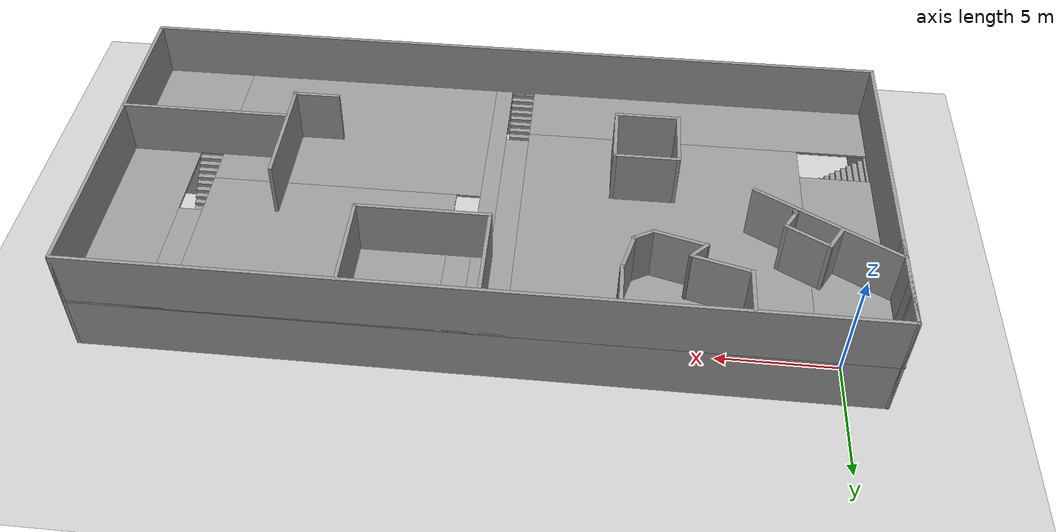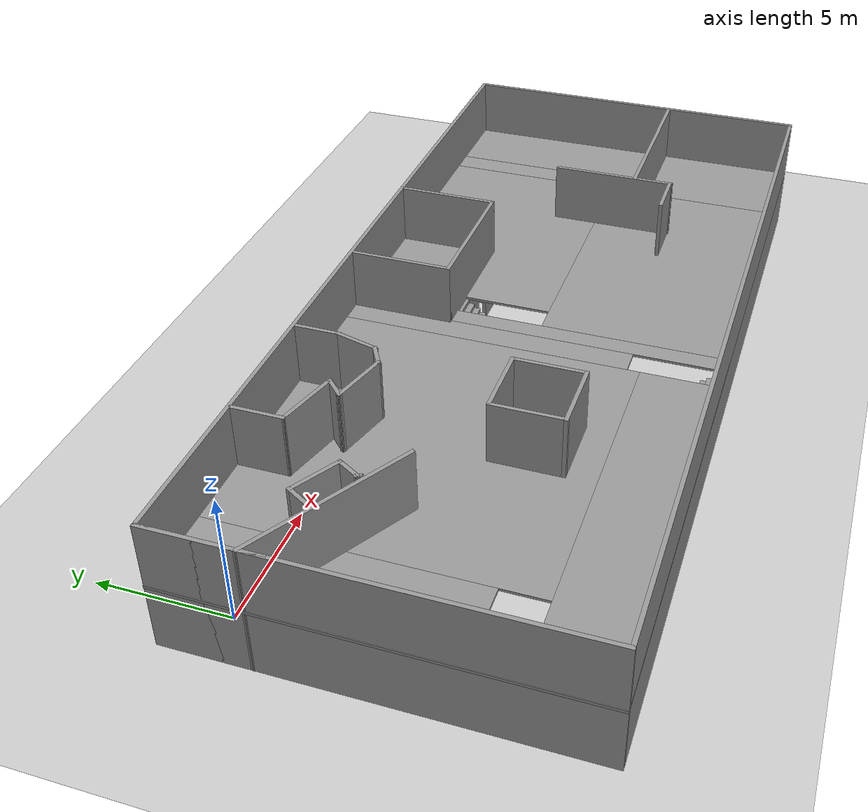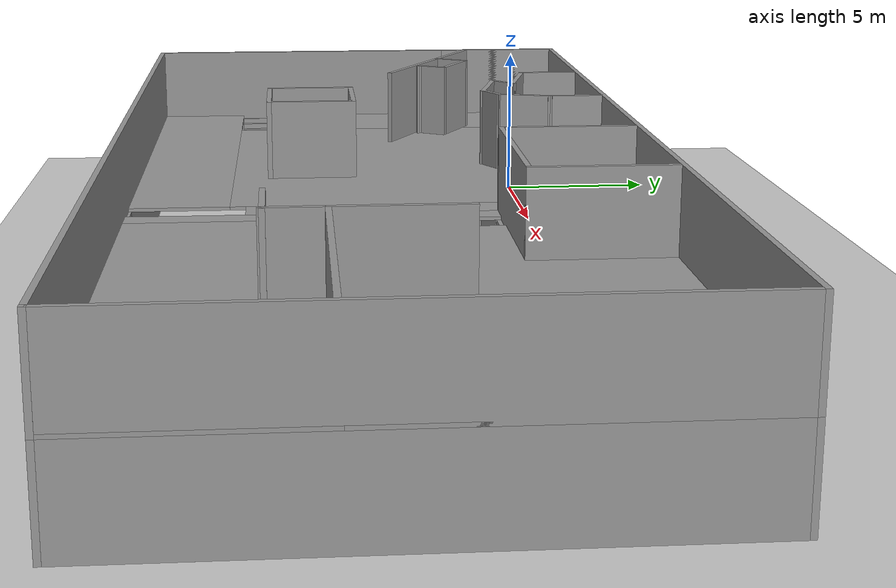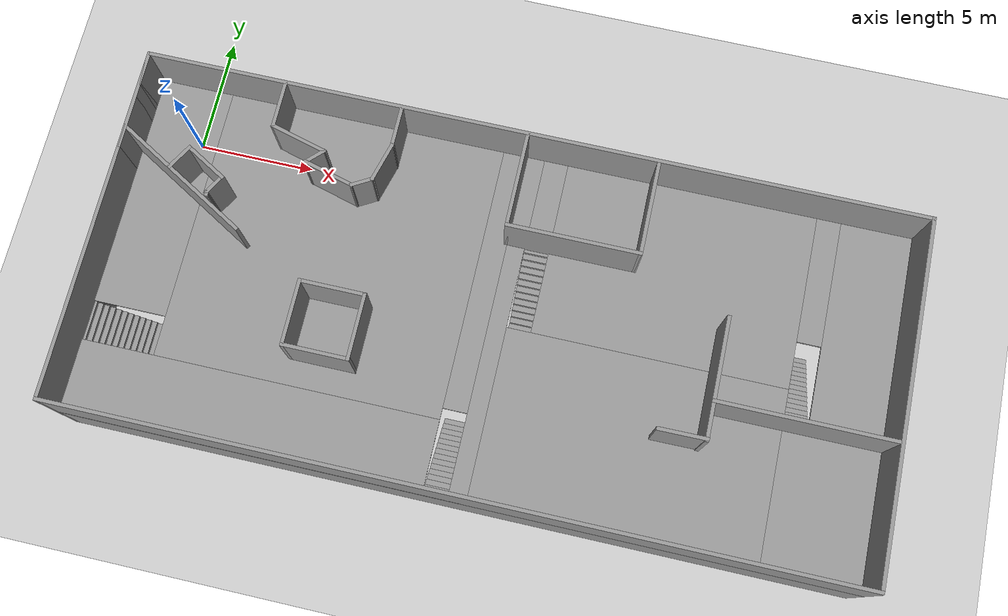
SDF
<sdf version="1.7">
 <world name="default">
  <light name="sun" type="directional">
   <pose>0 0 10 0 -0 0</pose>
   <diffuse>0.8 0.8 0.8 1</diffuse>
   <specular>0.2 0.2 0.2 1</specular>
   <attenuation>
    <range>1000</range>
    <constant>0.9</constant>
    <linear>0.01</linear>
    <quadratic>0.001</quadratic>
   </attenuation>
   <direction>-0.5 0.1 -0.9</direction>
   <spot><inner_angle>0</inner_angle><outer_angle>0</outer_angle><falloff>0</falloff></spot>
  </light>
  <model name="ground_plane">
   <static>1</static>
   <link name="link">
    <collision name="collision">
     <geometry><plane><normal>0 0 1</normal><size>100 100</size></plane></geometry>
     <surface><friction><ode><mu>100</mu><mu2>50</mu2></ode></friction></surface>
    </collision>
    <visual name="visual">
     <cast_shadows>0</cast_shadows>
     <geometry><plane><normal>0 0 1</normal><size>100 100</size></plane></geometry>
     <material>
      <script><uri>file://media/materials/scripts/gazebo.material</uri><name>Gazebo/Grey</name></script>
     </material>
    </visual>
   </link>
  </model>
  <gravity>0 0 -9.8</gravity>
  <magnetic_field>6e-06 2.3e-05 -4.2e-05</magnetic_field>
  <atmosphere type="adiabatic"/>
  <physics name="default_physics" default="0" type="ode">
   <max_step_size>0.004</max_step_size>
   <real_time_factor>1</real_time_factor>
   <real_time_update_rate>250</real_time_update_rate>
  </physics>
  <scene><ambient>0.4 0.4 0.4 1</ambient><background>0.7 0.7 0.7 1</background><shadows>1</shadows></scene>
  <spherical_coordinates>
   <surface_model>EARTH_WGS84</surface_model>
   <latitude_deg>0</latitude_deg>
   <longitude_deg>0</longitude_deg>
   <elevation>0</elevation>
   <heading_deg>0</heading_deg>
  </spherical_coordinates>
  <model name="room_with_stairs">
   <pose>14.4299 -5.56754 0 0 -0 0</pose>
   <link name="Floor_0">
    <pose>-1e-06 0 2.5 0 -0 0</pose>
    <visual name="Floor_0_Visual_0">
     <pose>-16.1009 0 0.05 0 -0 0</pose>
     <geometry><box><size>0.075725 14.75 0.1</size></box></geometry>
     <material>
      <script><uri>file://media/materials/scripts/gazebo.material</uri><name>Gazebo/Grey</name></script>
      <ambient>1 1 1 1</ambient>
     </material>
     <meta><layer>1</layer></meta>
    </visual>
    <collision name="Floor_0_Collision_0">
     <geometry><box><size>0.075725 14.75 0.1</size></box></geometry>
     <pose>-16.1009 0 0.05 0 -0 0</pose>
    </collision>
    <visual name="Floor_0_Visual_1">
     <pose>0.183693 0 0.05 0 -0 0</pose>
     <geometry><box><size>0.743302 14.75 0.1</size></box></geometry>
     <material>
      <script><uri>file://media/materials/scripts/gazebo.material</uri><name>Gazebo/Grey</name></script>
      <ambient>1 1 1 1</ambient>
     </material>
     <meta><layer>1</layer></meta>
    </visual>
    <collision name="Floor_0_Collision_1">
     <geometry><box><size>0.743302 14.75 0.1</size></box></geometry>
     <pose>0.183693 0 0.05 0 -0 0</pose>
    </collision>
    <visual name="Floor_0_Visual_2">
     <pose>-8.62548 -5.85906 0.05 0 -0 0</pose>
     <geometry><box><size>14.875 3.03188 0.1</size></box></geometry>
     <material>
      <script><uri>file://media/materials/scripts/gazebo.material</uri><name>Gazebo/Grey</name></script>
      <ambient>1 1 1 1</ambient>
     </material>
     <meta><layer>1</layer></meta>
    </visual>
    <collision name="Floor_0_Collision_2">
     <geometry><box><size>14.875 3.03188 0.1</size></box></geometry>
     <pose>-8.62548 -5.85906 0.05 0 -0 0</pose>
    </collision>
    <visual name="Floor_0_Visual_3">
     <pose>6.30013 -3.74051 0.05 0 -0 0</pose>
     <geometry><box><size>11.4896 7.26898 0.1</size></box></geometry>
     <material>
      <script><uri>file://media/materials/scripts/gazebo.material</uri><name>Gazebo/Grey</name></script>
      <ambient>1 1 1 1</ambient>
     </material>
     <meta><layer>1</layer></meta>
    </visual>
    <collision name="Floor_0_Collision_3">
     <geometry><box><size>11.4896 7.26898 0.1</size></box></geometry>
     <pose>6.30013 -3.74051 0.05 0 -0 0</pose>
    </collision>
    <visual name="Floor_0_Visual_4">
     <pose>-0.687958 -7.37454 0.05 0 -0 0</pose>
     <geometry><box><size>1 0.000917 0.1</size></box></geometry>
     <material>
      <script><uri>file://media/materials/scripts/gazebo.material</uri><name>Gazebo/Grey</name></script>
      <ambient>1 1 1 1</ambient>
     </material>
     <meta><layer>1</layer></meta>
    </visual>
    <collision name="Floor_0_Collision_4">
     <geometry><box><size>1 0.000917 0.1</size></box></geometry>
     <pose>-0.687958 -7.37454 0.05 0 -0 0</pose>
    </collision>
    <visual name="Floor_0_Visual_5">
     <pose>14.0918 -4.49895 0.05 0 -0 0</pose>
     <geometry><box><size>4.09381 5.7521 0.1</size></box></geometry>
     <material>
      <script><uri>file://media/materials/scripts/gazebo.material</uri><name>Gazebo/Grey</name></script>
      <ambient>1 1 1 1</ambient>
     </material>
     <meta><layer>1</layer></meta>
    </visual>
    <collision name="Floor_0_Collision_5">
     <geometry><box><size>4.09381 5.7521 0.1</size></box></geometry>
     <pose>14.0918 -4.49895 0.05 0 -0 0</pose>
    </collision>
    <visual name="Floor_0_Visual_6">
     <pose>-7.07815 1.51594 0.05 0 -0 0</pose>
     <geometry><box><size>11.7804 11.7181 0.1</size></box></geometry>
     <material>
      <script><uri>file://media/materials/scripts/gazebo.material</uri><name>Gazebo/Grey</name></script>
      <ambient>1 1 1 1</ambient>
     </material>
     <meta><layer>1</layer></meta>
    </visual>
    <collision name="Floor_0_Collision_6">
     <geometry><box><size>11.7804 11.7181 0.1</size></box></geometry>
     <pose>-7.07815 1.51594 0.05 0 -0 0</pose>
    </collision>
    <visual name="Floor_0_Visual_7">
     <pose>-0.687958 1.75046 0.05 0 -0 0</pose>
     <geometry><box><size>1 11.2491 0.1</size></box></geometry>
     <material>
      <script><uri>file://media/materials/scripts/gazebo.material</uri><name>Gazebo/Grey</name></script>
      <ambient>1 1 1 1</ambient>
     </material>
     <meta><layer>1</layer></meta>
    </visual>
    <collision name="Floor_0_Collision_7">
     <geometry><box><size>1 11.2491 0.1</size></box></geometry>
     <pose>-0.687958 1.75046 0.05 0 -0 0</pose>
    </collision>
    <visual name="Floor_0_Visual_8">
     <pose>-14.5157 2.33638 0.05 0 -0 0</pose>
     <geometry><box><size>3.09467 10.0772 0.1</size></box></geometry>
     <material>
      <script><uri>file://media/materials/scripts/gazebo.material</uri><name>Gazebo/Grey</name></script>
      <ambient>1 1 1 1</ambient>
     </material>
     <meta><layer>1</layer></meta>
    </visual>
    <collision name="Floor_0_Collision_8">
     <geometry><box><size>3.09467 10.0772 0.1</size></box></geometry>
     <pose>-14.5157 2.33638 0.05 0 -0 0</pose>
    </collision>
    <visual name="Floor_0_Visual_9">
     <pose>14.5918 2.87605 0.05 0 -0 0</pose>
     <geometry><box><size>3.09381 8.9979 0.1</size></box></geometry>
     <material>
      <script><uri>file://media/materials/scripts/gazebo.material</uri><name>Gazebo/Grey</name></script>
      <ambient>1 1 1 1</ambient>
     </material>
     <meta><layer>1</layer></meta>
    </visual>
    <collision name="Floor_0_Collision_9">
     <geometry><box><size>3.09381 8.9979 0.1</size></box></geometry>
     <pose>14.5918 2.87605 0.05 0 -0 0</pose>
    </collision>
    <visual name="Floor_0_Visual_10">
     <pose>6.80013 3.63449 0.05 0 -0 0</pose>
     <geometry><box><size>10.4896 7.48102 0.1</size></box></geometry>
     <material>
      <script><uri>file://media/materials/scripts/gazebo.material</uri><name>Gazebo/Grey</name></script>
      <ambient>1 1 1 1</ambient>
     </material>
     <meta><layer>1</layer></meta>
    </visual>
    <collision name="Floor_0_Collision_10">
     <geometry><box><size>10.4896 7.48102 0.1</size></box></geometry>
     <pose>6.80013 3.63449 0.05 0 -0 0</pose>
    </collision>
    <visual name="Floor_0_Visual_11">
     <pose>12.5449 4.62605 0.05 0 -0 0</pose>
     <geometry><box><size>1 5.4979 0.1</size></box></geometry>
     <material>
      <script><uri>file://media/materials/scripts/gazebo.material</uri><name>Gazebo/Grey</name></script>
      <ambient>1 1 1 1</ambient>
     </material>
     <meta><layer>1</layer></meta>
    </visual>
    <collision name="Floor_0_Collision_11">
     <geometry><box><size>1 5.4979 0.1</size></box></geometry>
     <pose>12.5449 4.62605 0.05 0 -0 0</pose>
    </collision>
    <visual name="Floor_0_Visual_12">
     <pose>1.05534 5.38449 0.05 0 -0 0</pose>
     <geometry><box><size>1 3.98102 0.1</size></box></geometry>
     <material>
      <script><uri>file://media/materials/scripts/gazebo.material</uri><name>Gazebo/Grey</name></script>
      <ambient>1 1 1 1</ambient>
     </material>
     <meta><layer>1</layer></meta>
    </visual>
    <collision name="Floor_0_Collision_12">
     <geometry><box><size>1 3.98102 0.1</size></box></geometry>
     <pose>1.05534 5.38449 0.05 0 -0 0</pose>
    </collision>
   </link>
   <link name="Stairs_0">
    <visual name="Stairs_0_Visual_0">
     <pose>-0.687958 -3.99075 0.083333 0 -0 0</pose>
     <geometry><box><size>1 0.233333 0.166667</size></box></geometry>
     <material>
      <script><uri>file://media/materials/scripts/gazebo.material</uri><name>Gazebo/Grey</name></script>
      <ambient>1 1 1 1</ambient>
     </material>
     <meta><layer>0</layer></meta>
    </visual>
    <collision name="Stairs_0_Collision_0">
     <geometry><box><size>1 0.233333 0.166667</size></box></geometry>
     <pose>-0.687958 -3.99075 0.083333 0 -0 0</pose>
    </collision>
    <visual name="Stairs_0_Visual_1">
     <pose>-0.687958 -4.22408 0.25 0 -0 0</pose>
     <geometry><box><size>1 0.233333 0.166667</size></box></geometry>
     <material>
      <script><uri>file://media/materials/scripts/gazebo.material</uri><name>Gazebo/Grey</name></script>
      <ambient>1 1 1 1</ambient>
     </material>
     <meta><layer>0</layer></meta>
    </visual>
    <collision name="Stairs_0_Collision_1">
     <geometry><box><size>1 0.233333 0.166667</size></box></geometry>
     <pose>-0.687958 -4.22408 0.25 0 -0 0</pose>
    </collision>
    <visual name="Stairs_0_Visual_2">
     <pose>-0.687958 -4.45742 0.416667 0 -0 0</pose>
     <geometry><box><size>1 0.233333 0.166667</size></box></geometry>
     <material>
      <script><uri>file://media/materials/scripts/gazebo.material</uri><name>Gazebo/Grey</name></script>
      <ambient>1 1 1 1</ambient>
     </material>
     <meta><layer>0</layer></meta>
    </visual>
    <collision name="Stairs_0_Collision_2">
     <geometry><box><size>1 0.233333 0.166667</size></box></geometry>
     <pose>-0.687958 -4.45742 0.416667 0 -0 0</pose>
    </collision>
    <visual name="Stairs_0_Visual_3">
     <pose>-0.687958 -4.69075 0.583333 0 -0 0</pose>
     <geometry><box><size>1 0.233333 0.166667</size></box></geometry>
     <material>
      <script><uri>file://media/materials/scripts/gazebo.material</uri><name>Gazebo/Grey</name></script>
      <ambient>1 1 1 1</ambient>
     </material>
     <meta><layer>0</layer></meta>
    </visual>
    <collision name="Stairs_0_Collision_3">
     <geometry><box><size>1 0.233333 0.166667</size></box></geometry>
     <pose>-0.687958 -4.69075 0.583333 0 -0 0</pose>
    </collision>
    <visual name="Stairs_0_Visual_4">
     <pose>-0.687958 -4.92408 0.75 0 -0 0</pose>
     <geometry><box><size>1 0.233333 0.166667</size></box></geometry>
     <material>
      <script><uri>file://media/materials/scripts/gazebo.material</uri><name>Gazebo/Grey</name></script>
      <ambient>1 1 1 1</ambient>
     </material>
     <meta><layer>0</layer></meta>
    </visual>
    <collision name="Stairs_0_Collision_4">
     <geometry><box><size>1 0.233333 0.166667</size></box></geometry>
     <pose>-0.687958 -4.92408 0.75 0 -0 0</pose>
    </collision>
    <visual name="Stairs_0_Visual_5">
     <pose>-0.687958 -5.15742 0.916667 0 -0 0</pose>
     <geometry><box><size>1 0.233333 0.166667</size></box></geometry>
     <material>
      <script><uri>file://media/materials/scripts/gazebo.material</uri><name>Gazebo/Grey</name></script>
      <ambient>1 1 1 1</ambient>
     </material>
     <meta><layer>0</layer></meta>
    </visual>
    <collision name="Stairs_0_Collision_5">
     <geometry><box><size>1 0.233333 0.166667</size></box></geometry>
     <pose>-0.687958 -5.15742 0.916667 0 -0 0</pose>
    </collision>
    <visual name="Stairs_0_Visual_6">
     <pose>-0.687958 -5.39075 1.08333 0 -0 0</pose>
     <geometry><box><size>1 0.233333 0.166667</size></box></geometry>
     <material>
      <script><uri>file://media/materials/scripts/gazebo.material</uri><name>Gazebo/Grey</name></script>
      <ambient>1 1 1 1</ambient>
     </material>
     <meta><layer>0</layer></meta>
    </visual>
    <collision name="Stairs_0_Collision_6">
     <geometry><box><size>1 0.233333 0.166667</size></box></geometry>
     <pose>-0.687958 -5.39075 1.08333 0 -0 0</pose>
    </collision>
    <visual name="Stairs_0_Visual_7">
     <pose>-0.687958 -5.62408 1.25 0 -0 0</pose>
     <geometry><box><size>1 0.233333 0.166667</size></box></geometry>
     <material>
      <script><uri>file://media/materials/scripts/gazebo.material</uri><name>Gazebo/Grey</name></script>
      <ambient>1 1 1 1</ambient>
     </material>
     <meta><layer>0</layer></meta>
    </visual>
    <collision name="Stairs_0_Collision_7">
     <geometry><box><size>1 0.233333 0.166667</size></box></geometry>
     <pose>-0.687958 -5.62408 1.25 0 -0 0</pose>
    </collision>
    <visual name="Stairs_0_Visual_8">
     <pose>-0.687958 -5.85742 1.41667 0 -0 0</pose>
     <geometry><box><size>1 0.233333 0.166667</size></box></geometry>
     <material>
      <script><uri>file://media/materials/scripts/gazebo.material</uri><name>Gazebo/Grey</name></script>
      <ambient>1 1 1 1</ambient>
     </material>
     <meta><layer>0</layer></meta>
    </visual>
    <collision name="Stairs_0_Collision_8">
     <geometry><box><size>1 0.233333 0.166667</size></box></geometry>
     <pose>-0.687958 -5.85742 1.41667 0 -0 0</pose>
    </collision>
    <visual name="Stairs_0_Visual_9">
     <pose>-0.687958 -6.09075 1.58333 0 -0 0</pose>
     <geometry><box><size>1 0.233333 0.166667</size></box></geometry>
     <material>
      <script><uri>file://media/materials/scripts/gazebo.material</uri><name>Gazebo/Grey</name></script>
      <ambient>1 1 1 1</ambient>
     </material>
     <meta><layer>0</layer></meta>
    </visual>
    <collision name="Stairs_0_Collision_9">
     <geometry><box><size>1 0.233333 0.166667</size></box></geometry>
     <pose>-0.687958 -6.09075 1.58333 0 -0 0</pose>
    </collision>
    <visual name="Stairs_0_Visual_10">
     <pose>-0.687958 -6.32408 1.75 0 -0 0</pose>
     <geometry><box><size>1 0.233333 0.166667</size></box></geometry>
     <material>
      <script><uri>file://media/materials/scripts/gazebo.material</uri><name>Gazebo/Grey</name></script>
      <ambient>1 1 1 1</ambient>
     </material>
     <meta><layer>0</layer></meta>
    </visual>
    <collision name="Stairs_0_Collision_10">
     <geometry><box><size>1 0.233333 0.166667</size></box></geometry>
     <pose>-0.687958 -6.32408 1.75 0 -0 0</pose>
    </collision>
    <visual name="Stairs_0_Visual_11">
     <pose>-0.687958 -6.55742 1.91667 0 -0 0</pose>
     <geometry><box><size>1 0.233333 0.166667</size></box></geometry>
     <material>
      <script><uri>file://media/materials/scripts/gazebo.material</uri><name>Gazebo/Grey</name></script>
      <ambient>1 1 1 1</ambient>
     </material>
     <meta><layer>0</layer></meta>
    </visual>
    <collision name="Stairs_0_Collision_11">
     <geometry><box><size>1 0.233333 0.166667</size></box></geometry>
     <pose>-0.687958 -6.55742 1.91667 0 -0 0</pose>
    </collision>
    <visual name="Stairs_0_Visual_12">
     <pose>-0.687958 -6.79075 2.08333 0 -0 0</pose>
     <geometry><box><size>1 0.233333 0.166667</size></box></geometry>
     <material>
      <script><uri>file://media/materials/scripts/gazebo.material</uri><name>Gazebo/Grey</name></script>
      <ambient>1 1 1 1</ambient>
     </material>
     <meta><layer>0</layer></meta>
    </visual>
    <collision name="Stairs_0_Collision_12">
     <geometry><box><size>1 0.233333 0.166667</size></box></geometry>
     <pose>-0.687958 -6.79075 2.08333 0 -0 0</pose>
    </collision>
    <visual name="Stairs_0_Visual_13">
     <pose>-0.687958 -7.02408 2.25 0 -0 0</pose>
     <geometry><box><size>1 0.233333 0.166667</size></box></geometry>
     <material>
      <script><uri>file://media/materials/scripts/gazebo.material</uri><name>Gazebo/Grey</name></script>
      <ambient>1 1 1 1</ambient>
     </material>
     <meta><layer>0</layer></meta>
    </visual>
    <collision name="Stairs_0_Collision_13">
     <geometry><box><size>1 0.233333 0.166667</size></box></geometry>
     <pose>-0.687958 -7.02408 2.25 0 -0 0</pose>
    </collision>
    <visual name="Stairs_0_Visual_14">
     <pose>-0.687958 -7.25742 2.41667 0 -0 0</pose>
     <geometry><box><size>1 0.233333 0.166667</size></box></geometry>
     <material>
      <script><uri>file://media/materials/scripts/gazebo.material</uri><name>Gazebo/Grey</name></script>
      <ambient>1 1 1 1</ambient>
     </material>
     <meta><layer>0</layer></meta>
    </visual>
    <collision name="Stairs_0_Collision_14">
     <geometry><box><size>1 0.233333 0.166667</size></box></geometry>
     <pose>-0.687958 -7.25742 2.41667 0 -0 0</pose>
    </collision>
   </link>
   <link name="Stairs_1">
    <visual name="Stairs_1_Visual_0">
     <pose>-13.0715 -3.52268 0.083333 0 -0 -1.5708</pose>
     <geometry><box><size>1.64089 0.206311 0.166667</size></box></geometry>
     <material>
      <script><uri>file://media/materials/scripts/gazebo.material</uri><name>Gazebo/Grey</name></script>
      <ambient>1 1 1 1</ambient>
     </material>
     <meta><layer>0</layer></meta>
    </visual>
    <collision name="Stairs_1_Collision_0">
     <geometry><box><size>1.64089 0.206311 0.166667</size></box></geometry>
     <pose>-13.0715 -3.52268 0.083333 0 -0 -1.5708</pose>
    </collision>
    <visual name="Stairs_1_Visual_1">
     <pose>-13.2778 -3.52268 0.25 0 -0 -1.5708</pose>
     <geometry><box><size>1.64089 0.206311 0.166667</size></box></geometry>
     <material>
      <script><uri>file://media/materials/scripts/gazebo.material</uri><name>Gazebo/Grey</name></script>
      <ambient>1 1 1 1</ambient>
     </material>
     <meta><layer>0</layer></meta>
    </visual>
    <collision name="Stairs_1_Collision_1">
     <geometry><box><size>1.64089 0.206311 0.166667</size></box></geometry>
     <pose>-13.2778 -3.52268 0.25 0 -0 -1.5708</pose>
    </collision>
    <visual name="Stairs_1_Visual_2">
     <pose>-13.4841 -3.52268 0.416667 0 -0 -1.5708</pose>
     <geometry><box><size>1.64089 0.206311 0.166667</size></box></geometry>
     <material>
      <script><uri>file://media/materials/scripts/gazebo.material</uri><name>Gazebo/Grey</name></script>
      <ambient>1 1 1 1</ambient>
     </material>
     <meta><layer>0</layer></meta>
    </visual>
    <collision name="Stairs_1_Collision_2">
     <geometry><box><size>1.64089 0.206311 0.166667</size></box></geometry>
     <pose>-13.4841 -3.52268 0.416667 0 -0 -1.5708</pose>
    </collision>
    <visual name="Stairs_1_Visual_3">
     <pose>-13.6904 -3.52268 0.583333 0 -0 -1.5708</pose>
     <geometry><box><size>1.64089 0.206311 0.166667</size></box></geometry>
     <material>
      <script><uri>file://media/materials/scripts/gazebo.material</uri><name>Gazebo/Grey</name></script>
      <ambient>1 1 1 1</ambient>
     </material>
     <meta><layer>0</layer></meta>
    </visual>
    <collision name="Stairs_1_Collision_3">
     <geometry><box><size>1.64089 0.206311 0.166667</size></box></geometry>
     <pose>-13.6904 -3.52268 0.583333 0 -0 -1.5708</pose>
    </collision>
    <visual name="Stairs_1_Visual_4">
     <pose>-13.8967 -3.52268 0.75 0 -0 -1.5708</pose>
     <geometry><box><size>1.64089 0.206311 0.166667</size></box></geometry>
     <material>
      <script><uri>file://media/materials/scripts/gazebo.material</uri><name>Gazebo/Grey</name></script>
      <ambient>1 1 1 1</ambient>
     </material>
     <meta><layer>0</layer></meta>
    </visual>
    <collision name="Stairs_1_Collision_4">
     <geometry><box><size>1.64089 0.206311 0.166667</size></box></geometry>
     <pose>-13.8967 -3.52268 0.75 0 -0 -1.5708</pose>
    </collision>
    <visual name="Stairs_1_Visual_5">
     <pose>-14.103 -3.52268 0.916667 0 -0 -1.5708</pose>
     <geometry><box><size>1.64089 0.206311 0.166667</size></box></geometry>
     <material>
      <script><uri>file://media/materials/scripts/gazebo.material</uri><name>Gazebo/Grey</name></script>
      <ambient>1 1 1 1</ambient>
     </material>
     <meta><layer>0</layer></meta>
    </visual>
    <collision name="Stairs_1_Collision_5">
     <geometry><box><size>1.64089 0.206311 0.166667</size></box></geometry>
     <pose>-14.103 -3.52268 0.916667 0 -0 -1.5708</pose>
    </collision>
    <visual name="Stairs_1_Visual_6">
     <pose>-14.3094 -3.52268 1.08333 0 -0 -1.5708</pose>
     <geometry><box><size>1.64089 0.206311 0.166667</size></box></geometry>
     <material>
      <script><uri>file://media/materials/scripts/gazebo.material</uri><name>Gazebo/Grey</name></script>
      <ambient>1 1 1 1</ambient>
     </material>
     <meta><layer>0</layer></meta>
    </visual>
    <collision name="Stairs_1_Collision_6">
     <geometry><box><size>1.64089 0.206311 0.166667</size></box></geometry>
     <pose>-14.3094 -3.52268 1.08333 0 -0 -1.5708</pose>
    </collision>
    <visual name="Stairs_1_Visual_7">
     <pose>-14.5157 -3.52268 1.25 0 -0 -1.5708</pose>
     <geometry><box><size>1.64089 0.206311 0.166667</size></box></geometry>
     <material>
      <script><uri>file://media/materials/scripts/gazebo.material</uri><name>Gazebo/Grey</name></script>
      <ambient>1 1 1 1</ambient>
     </material>
     <meta><layer>0</layer></meta>
    </visual>
    <collision name="Stairs_1_Collision_7">
     <geometry><box><size>1.64089 0.206311 0.166667</size></box></geometry>
     <pose>-14.5157 -3.52268 1.25 0 -0 -1.5708</pose>
    </collision>
    <visual name="Stairs_1_Visual_8">
     <pose>-14.722 -3.52268 1.41667 0 -0 -1.5708</pose>
     <geometry><box><size>1.64089 0.206311 0.166667</size></box></geometry>
     <material>
      <script><uri>file://media/materials/scripts/gazebo.material</uri><name>Gazebo/Grey</name></script>
      <ambient>1 1 1 1</ambient>
     </material>
     <meta><layer>0</layer></meta>
    </visual>
    <collision name="Stairs_1_Collision_8">
     <geometry><box><size>1.64089 0.206311 0.166667</size></box></geometry>
     <pose>-14.722 -3.52268 1.41667 0 -0 -1.5708</pose>
    </collision>
    <visual name="Stairs_1_Visual_9">
     <pose>-14.9283 -3.52268 1.58333 0 -0 -1.5708</pose>
     <geometry><box><size>1.64089 0.206311 0.166667</size></box></geometry>
     <material>
      <script><uri>file://media/materials/scripts/gazebo.material</uri><name>Gazebo/Grey</name></script>
      <ambient>1 1 1 1</ambient>
     </material>
     <meta><layer>0</layer></meta>
    </visual>
    <collision name="Stairs_1_Collision_9">
     <geometry><box><size>1.64089 0.206311 0.166667</size></box></geometry>
     <pose>-14.9283 -3.52268 1.58333 0 -0 -1.5708</pose>
    </collision>
    <visual name="Stairs_1_Visual_10">
     <pose>-15.1346 -3.52268 1.75 0 -0 -1.5708</pose>
     <geometry><box><size>1.64089 0.206311 0.166667</size></box></geometry>
     <material>
      <script><uri>file://media/materials/scripts/gazebo.material</uri><name>Gazebo/Grey</name></script>
      <ambient>1 1 1 1</ambient>
     </material>
     <meta><layer>0</layer></meta>
    </visual>
    <collision name="Stairs_1_Collision_10">
     <geometry><box><size>1.64089 0.206311 0.166667</size></box></geometry>
     <pose>-15.1346 -3.52268 1.75 0 -0 -1.5708</pose>
    </collision>
    <visual name="Stairs_1_Visual_11">
     <pose>-15.3409 -3.52268 1.91667 0 -0 -1.5708</pose>
     <geometry><box><size>1.64089 0.206311 0.166667</size></box></geometry>
     <material>
      <script><uri>file://media/materials/scripts/gazebo.material</uri><name>Gazebo/Grey</name></script>
      <ambient>1 1 1 1</ambient>
     </material>
     <meta><layer>0</layer></meta>
    </visual>
    <collision name="Stairs_1_Collision_11">
     <geometry><box><size>1.64089 0.206311 0.166667</size></box></geometry>
     <pose>-15.3409 -3.52268 1.91667 0 -0 -1.5708</pose>
    </collision>
    <visual name="Stairs_1_Visual_12">
     <pose>-15.5472 -3.52268 2.08333 0 -0 -1.5708</pose>
     <geometry><box><size>1.64089 0.206311 0.166667</size></box></geometry>
     <material>
      <script><uri>file://media/materials/scripts/gazebo.material</uri><name>Gazebo/Grey</name></script>
      <ambient>1 1 1 1</ambient>
     </material>
     <meta><layer>0</layer></meta>
    </visual>
    <collision name="Stairs_1_Collision_12">
     <geometry><box><size>1.64089 0.206311 0.166667</size></box></geometry>
     <pose>-15.5472 -3.52268 2.08333 0 -0 -1.5708</pose>
    </collision>
    <visual name="Stairs_1_Visual_13">
     <pose>-15.7535 -3.52268 2.25 0 -0 -1.5708</pose>
     <geometry><box><size>1.64089 0.206311 0.166667</size></box></geometry>
     <material>
      <script><uri>file://media/materials/scripts/gazebo.material</uri><name>Gazebo/Grey</name></script>
      <ambient>1 1 1 1</ambient>
     </material>
     <meta><layer>0</layer></meta>
    </visual>
    <collision name="Stairs_1_Collision_13">
     <geometry><box><size>1.64089 0.206311 0.166667</size></box></geometry>
     <pose>-15.7535 -3.52268 2.25 0 -0 -1.5708</pose>
    </collision>
    <visual name="Stairs_1_Visual_14">
     <pose>-15.9598 -3.52268 2.41667 0 -0 -1.5708</pose>
     <geometry><box><size>1.64089 0.206311 0.166667</size></box></geometry>
     <material>
      <script><uri>file://media/materials/scripts/gazebo.material</uri><name>Gazebo/Grey</name></script>
      <ambient>1 1 1 1</ambient>
     </material>
     <meta><layer>0</layer></meta>
    </visual>
    <collision name="Stairs_1_Collision_14">
     <geometry><box><size>1.64089 0.206311 0.166667</size></box></geometry>
     <pose>-15.9598 -3.52268 2.41667 0 -0 -1.5708</pose>
    </collision>
   </link>
   <link name="Stairs_2">
    <visual name="Stairs_2_Visual_0">
     <pose>1.05534 0.01065 0.083333 0 -0 -3.14159</pose>
     <geometry><box><size>1 0.233333 0.166667</size></box></geometry>
     <material>
      <script><uri>file://media/materials/scripts/gazebo.material</uri><name>Gazebo/Grey</name></script>
      <ambient>1 1 1 1</ambient>
     </material>
     <meta><layer>0</layer></meta>
    </visual>
    <collision name="Stairs_2_Collision_0">
     <geometry><box><size>1 0.233333 0.166667</size></box></geometry>
     <pose>1.05534 0.01065 0.083333 0 -0 -3.14159</pose>
    </collision>
    <visual name="Stairs_2_Visual_1">
     <pose>1.05534 0.243983 0.25 0 -0 -3.14159</pose>
     <geometry><box><size>1 0.233333 0.166667</size></box></geometry>
     <material>
      <script><uri>file://media/materials/scripts/gazebo.material</uri><name>Gazebo/Grey</name></script>
      <ambient>1 1 1 1</ambient>
     </material>
     <meta><layer>0</layer></meta>
    </visual>
    <collision name="Stairs_2_Collision_1">
     <geometry><box><size>1 0.233333 0.166667</size></box></geometry>
     <pose>1.05534 0.243983 0.25 0 -0 -3.14159</pose>
    </collision>
    <visual name="Stairs_2_Visual_2">
     <pose>1.05534 0.477316 0.416667 0 -0 -3.14159</pose>
     <geometry><box><size>1 0.233333 0.166667</size></box></geometry>
     <material>
      <script><uri>file://media/materials/scripts/gazebo.material</uri><name>Gazebo/Grey</name></script>
      <ambient>1 1 1 1</ambient>
     </material>
     <meta><layer>0</layer></meta>
    </visual>
    <collision name="Stairs_2_Collision_2">
     <geometry><box><size>1 0.233333 0.166667</size></box></geometry>
     <pose>1.05534 0.477316 0.416667 0 -0 -3.14159</pose>
    </collision>
    <visual name="Stairs_2_Visual_3">
     <pose>1.05534 0.710649 0.583333 0 -0 -3.14159</pose>
     <geometry><box><size>1 0.233333 0.166667</size></box></geometry>
     <material>
      <script><uri>file://media/materials/scripts/gazebo.material</uri><name>Gazebo/Grey</name></script>
      <ambient>1 1 1 1</ambient>
     </material>
     <meta><layer>0</layer></meta>
    </visual>
    <collision name="Stairs_2_Collision_3">
     <geometry><box><size>1 0.233333 0.166667</size></box></geometry>
     <pose>1.05534 0.710649 0.583333 0 -0 -3.14159</pose>
    </collision>
    <visual name="Stairs_2_Visual_4">
     <pose>1.05534 0.943983 0.75 0 -0 -3.14159</pose>
     <geometry><box><size>1 0.233333 0.166667</size></box></geometry>
     <material>
      <script><uri>file://media/materials/scripts/gazebo.material</uri><name>Gazebo/Grey</name></script>
      <ambient>1 1 1 1</ambient>
     </material>
     <meta><layer>0</layer></meta>
    </visual>
    <collision name="Stairs_2_Collision_4">
     <geometry><box><size>1 0.233333 0.166667</size></box></geometry>
     <pose>1.05534 0.943983 0.75 0 -0 -3.14159</pose>
    </collision>
    <visual name="Stairs_2_Visual_5">
     <pose>1.05534 1.17732 0.916667 0 -0 -3.14159</pose>
     <geometry><box><size>1 0.233333 0.166667</size></box></geometry>
     <material>
      <script><uri>file://media/materials/scripts/gazebo.material</uri><name>Gazebo/Grey</name></script>
      <ambient>1 1 1 1</ambient>
     </material>
     <meta><layer>0</layer></meta>
    </visual>
    <collision name="Stairs_2_Collision_5">
     <geometry><box><size>1 0.233333 0.166667</size></box></geometry>
     <pose>1.05534 1.17732 0.916667 0 -0 -3.14159</pose>
    </collision>
    <visual name="Stairs_2_Visual_6">
     <pose>1.05534 1.41065 1.08333 0 -0 -3.14159</pose>
     <geometry><box><size>1 0.233333 0.166667</size></box></geometry>
     <material>
      <script><uri>file://media/materials/scripts/gazebo.material</uri><name>Gazebo/Grey</name></script>
      <ambient>1 1 1 1</ambient>
     </material>
     <meta><layer>0</layer></meta>
    </visual>
    <collision name="Stairs_2_Collision_6">
     <geometry><box><size>1 0.233333 0.166667</size></box></geometry>
     <pose>1.05534 1.41065 1.08333 0 -0 -3.14159</pose>
    </collision>
    <visual name="Stairs_2_Visual_7">
     <pose>1.05534 1.64398 1.25 0 -0 -3.14159</pose>
     <geometry><box><size>1 0.233333 0.166667</size></box></geometry>
     <material>
      <script><uri>file://media/materials/scripts/gazebo.material</uri><name>Gazebo/Grey</name></script>
      <ambient>1 1 1 1</ambient>
     </material>
     <meta><layer>0</layer></meta>
    </visual>
    <collision name="Stairs_2_Collision_7">
     <geometry><box><size>1 0.233333 0.166667</size></box></geometry>
     <pose>1.05534 1.64398 1.25 0 -0 -3.14159</pose>
    </collision>
    <visual name="Stairs_2_Visual_8">
     <pose>1.05534 1.87732 1.41667 0 -0 -3.14159</pose>
     <geometry><box><size>1 0.233333 0.166667</size></box></geometry>
     <material>
      <script><uri>file://media/materials/scripts/gazebo.material</uri><name>Gazebo/Grey</name></script>
      <ambient>1 1 1 1</ambient>
     </material>
     <meta><layer>0</layer></meta>
    </visual>
    <collision name="Stairs_2_Collision_8">
     <geometry><box><size>1 0.233333 0.166667</size></box></geometry>
     <pose>1.05534 1.87732 1.41667 0 -0 -3.14159</pose>
    </collision>
    <visual name="Stairs_2_Visual_9">
     <pose>1.05534 2.11065 1.58333 0 -0 -3.14159</pose>
     <geometry><box><size>1 0.233333 0.166667</size></box></geometry>
     <material>
      <script><uri>file://media/materials/scripts/gazebo.material</uri><name>Gazebo/Grey</name></script>
      <ambient>1 1 1 1</ambient>
     </material>
     <meta><layer>0</layer></meta>
    </visual>
    <collision name="Stairs_2_Collision_9">
     <geometry><box><size>1 0.233333 0.166667</size></box></geometry>
     <pose>1.05534 2.11065 1.58333 0 -0 -3.14159</pose>
    </collision>
    <visual name="Stairs_2_Visual_10">
     <pose>1.05534 2.34398 1.75 0 -0 -3.14159</pose>
     <geometry><box><size>1 0.233333 0.166667</size></box></geometry>
     <material>
      <script><uri>file://media/materials/scripts/gazebo.material</uri><name>Gazebo/Grey</name></script>
      <ambient>1 1 1 1</ambient>
     </material>
     <meta><layer>0</layer></meta>
    </visual>
    <collision name="Stairs_2_Collision_10">
     <geometry><box><size>1 0.233333 0.166667</size></box></geometry>
     <pose>1.05534 2.34398 1.75 0 -0 -3.14159</pose>
    </collision>
    <visual name="Stairs_2_Visual_11">
     <pose>1.05534 2.57732 1.91667 0 -0 -3.14159</pose>
     <geometry><box><size>1 0.233333 0.166667</size></box></geometry>
     <material>
      <script><uri>file://media/materials/scripts/gazebo.material</uri><name>Gazebo/Grey</name></script>
      <ambient>1 1 1 1</ambient>
     </material>
     <meta><layer>0</layer></meta>
    </visual>
    <collision name="Stairs_2_Collision_11">
     <geometry><box><size>1 0.233333 0.166667</size></box></geometry>
     <pose>1.05534 2.57732 1.91667 0 -0 -3.14159</pose>
    </collision>
    <visual name="Stairs_2_Visual_12">
     <pose>1.05534 2.81065 2.08333 0 -0 -3.14159</pose>
     <geometry><box><size>1 0.233333 0.166667</size></box></geometry>
     <material>
      <script><uri>file://media/materials/scripts/gazebo.material</uri><name>Gazebo/Grey</name></script>
      <ambient>1 1 1 1</ambient>
     </material>
     <meta><layer>0</layer></meta>
    </visual>
    <collision name="Stairs_2_Collision_12">
     <geometry><box><size>1 0.233333 0.166667</size></box></geometry>
     <pose>1.05534 2.81065 2.08333 0 -0 -3.14159</pose>
    </collision>
    <visual name="Stairs_2_Visual_13">
     <pose>1.05534 3.04398 2.25 0 -0 -3.14159</pose>
     <geometry><box><size>1 0.233333 0.166667</size></box></geometry>
     <material>
      <script><uri>file://media/materials/scripts/gazebo.material</uri><name>Gazebo/Grey</name></script>
      <ambient>1 1 1 1</ambient>
     </material>
     <meta><layer>0</layer></meta>
    </visual>
    <collision name="Stairs_2_Collision_13">
     <geometry><box><size>1 0.233333 0.166667</size></box></geometry>
     <pose>1.05534 3.04398 2.25 0 -0 -3.14159</pose>
    </collision>
    <visual name="Stairs_2_Visual_14">
     <pose>1.05534 3.27732 2.41667 0 -0 -3.14159</pose>
     <geometry><box><size>1 0.233333 0.166667</size></box></geometry>
     <material>
      <script><uri>file://media/materials/scripts/gazebo.material</uri><name>Gazebo/Grey</name></script>
      <ambient>1 1 1 1</ambient>
     </material>
     <meta><layer>0</layer></meta>
    </visual>
    <collision name="Stairs_2_Collision_14">
     <geometry><box><size>1 0.233333 0.166667</size></box></geometry>
     <pose>1.05534 3.27732 2.41667 0 -0 -3.14159</pose>
    </collision>
   </link>
   <link name="Stairs_3">
    <visual name="Stairs_3_Visual_0">
     <pose>12.5449 1.76044 0.083333 0 -0 0</pose>
     <geometry><box><size>1 0.233333 0.166667</size></box></geometry>
     <material>
      <script><uri>file://media/materials/scripts/gazebo.material</uri><name>Gazebo/Grey</name></script>
      <ambient>1 1 1 1</ambient>
     </material>
     <meta><layer>0</layer></meta>
    </visual>
    <collision name="Stairs_3_Collision_0">
     <geometry><box><size>1 0.233333 0.166667</size></box></geometry>
     <pose>12.5449 1.76044 0.083333 0 -0 0</pose>
    </collision>
    <visual name="Stairs_3_Visual_1">
     <pose>12.5449 1.5271 0.25 0 -0 0</pose>
     <geometry><box><size>1 0.233333 0.166667</size></box></geometry>
     <material>
      <script><uri>file://media/materials/scripts/gazebo.material</uri><name>Gazebo/Grey</name></script>
      <ambient>1 1 1 1</ambient>
     </material>
     <meta><layer>0</layer></meta>
    </visual>
    <collision name="Stairs_3_Collision_1">
     <geometry><box><size>1 0.233333 0.166667</size></box></geometry>
     <pose>12.5449 1.5271 0.25 0 -0 0</pose>
    </collision>
    <visual name="Stairs_3_Visual_2">
     <pose>12.5449 1.29377 0.416667 0 -0 0</pose>
     <geometry><box><size>1 0.233333 0.166667</size></box></geometry>
     <material>
      <script><uri>file://media/materials/scripts/gazebo.material</uri><name>Gazebo/Grey</name></script>
      <ambient>1 1 1 1</ambient>
     </material>
     <meta><layer>0</layer></meta>
    </visual>
    <collision name="Stairs_3_Collision_2">
     <geometry><box><size>1 0.233333 0.166667</size></box></geometry>
     <pose>12.5449 1.29377 0.416667 0 -0 0</pose>
    </collision>
    <visual name="Stairs_3_Visual_3">
     <pose>12.5449 1.06044 0.583333 0 -0 0</pose>
     <geometry><box><size>1 0.233333 0.166667</size></box></geometry>
     <material>
      <script><uri>file://media/materials/scripts/gazebo.material</uri><name>Gazebo/Grey</name></script>
      <ambient>1 1 1 1</ambient>
     </material>
     <meta><layer>0</layer></meta>
    </visual>
    <collision name="Stairs_3_Collision_3">
     <geometry><box><size>1 0.233333 0.166667</size></box></geometry>
     <pose>12.5449 1.06044 0.583333 0 -0 0</pose>
    </collision>
    <visual name="Stairs_3_Visual_4">
     <pose>12.5449 0.827104 0.75 0 -0 0</pose>
     <geometry><box><size>1 0.233333 0.166667</size></box></geometry>
     <material>
      <script><uri>file://media/materials/scripts/gazebo.material</uri><name>Gazebo/Grey</name></script>
      <ambient>1 1 1 1</ambient>
     </material>
     <meta><layer>0</layer></meta>
    </visual>
    <collision name="Stairs_3_Collision_4">
     <geometry><box><size>1 0.233333 0.166667</size></box></geometry>
     <pose>12.5449 0.827104 0.75 0 -0 0</pose>
    </collision>
    <visual name="Stairs_3_Visual_5">
     <pose>12.5449 0.593771 0.916667 0 -0 0</pose>
     <geometry><box><size>1 0.233333 0.166667</size></box></geometry>
     <material>
      <script><uri>file://media/materials/scripts/gazebo.material</uri><name>Gazebo/Grey</name></script>
      <ambient>1 1 1 1</ambient>
     </material>
     <meta><layer>0</layer></meta>
    </visual>
    <collision name="Stairs_3_Collision_5">
     <geometry><box><size>1 0.233333 0.166667</size></box></geometry>
     <pose>12.5449 0.593771 0.916667 0 -0 0</pose>
    </collision>
    <visual name="Stairs_3_Visual_6">
     <pose>12.5449 0.360437 1.08333 0 -0 0</pose>
     <geometry><box><size>1 0.233333 0.166667</size></box></geometry>
     <material>
      <script><uri>file://media/materials/scripts/gazebo.material</uri><name>Gazebo/Grey</name></script>
      <ambient>1 1 1 1</ambient>
     </material>
     <meta><layer>0</layer></meta>
    </visual>
    <collision name="Stairs_3_Collision_6">
     <geometry><box><size>1 0.233333 0.166667</size></box></geometry>
     <pose>12.5449 0.360437 1.08333 0 -0 0</pose>
    </collision>
    <visual name="Stairs_3_Visual_7">
     <pose>12.5449 0.127104 1.25 0 -0 0</pose>
     <geometry><box><size>1 0.233333 0.166667</size></box></geometry>
     <material>
      <script><uri>file://media/materials/scripts/gazebo.material</uri><name>Gazebo/Grey</name></script>
      <ambient>1 1 1 1</ambient>
     </material>
     <meta><layer>0</layer></meta>
    </visual>
    <collision name="Stairs_3_Collision_7">
     <geometry><box><size>1 0.233333 0.166667</size></box></geometry>
     <pose>12.5449 0.127104 1.25 0 -0 0</pose>
    </collision>
    <visual name="Stairs_3_Visual_8">
     <pose>12.5449 -0.106229 1.41667 0 -0 0</pose>
     <geometry><box><size>1 0.233333 0.166667</size></box></geometry>
     <material>
      <script><uri>file://media/materials/scripts/gazebo.material</uri><name>Gazebo/Grey</name></script>
      <ambient>1 1 1 1</ambient>
     </material>
     <meta><layer>0</layer></meta>
    </visual>
    <collision name="Stairs_3_Collision_8">
     <geometry><box><size>1 0.233333 0.166667</size></box></geometry>
     <pose>12.5449 -0.106229 1.41667 0 -0 0</pose>
    </collision>
    <visual name="Stairs_3_Visual_9">
     <pose>12.5449 -0.339562 1.58333 0 -0 0</pose>
     <geometry><box><size>1 0.233333 0.166667</size></box></geometry>
     <material>
      <script><uri>file://media/materials/scripts/gazebo.material</uri><name>Gazebo/Grey</name></script>
      <ambient>1 1 1 1</ambient>
     </material>
     <meta><layer>0</layer></meta>
    </visual>
    <collision name="Stairs_3_Collision_9">
     <geometry><box><size>1 0.233333 0.166667</size></box></geometry>
     <pose>12.5449 -0.339562 1.58333 0 -0 0</pose>
    </collision>
    <visual name="Stairs_3_Visual_10">
     <pose>12.5449 -0.572896 1.75 0 -0 0</pose>
     <geometry><box><size>1 0.233333 0.166667</size></box></geometry>
     <material>
      <script><uri>file://media/materials/scripts/gazebo.material</uri><name>Gazebo/Grey</name></script>
      <ambient>1 1 1 1</ambient>
     </material>
     <meta><layer>0</layer></meta>
    </visual>
    <collision name="Stairs_3_Collision_10">
     <geometry><box><size>1 0.233333 0.166667</size></box></geometry>
     <pose>12.5449 -0.572896 1.75 0 -0 0</pose>
    </collision>
    <visual name="Stairs_3_Visual_11">
     <pose>12.5449 -0.806229 1.91667 0 -0 0</pose>
     <geometry><box><size>1 0.233333 0.166667</size></box></geometry>
     <material>
      <script><uri>file://media/materials/scripts/gazebo.material</uri><name>Gazebo/Grey</name></script>
      <ambient>1 1 1 1</ambient>
     </material>
     <meta><layer>0</layer></meta>
    </visual>
    <collision name="Stairs_3_Collision_11">
     <geometry><box><size>1 0.233333 0.166667</size></box></geometry>
     <pose>12.5449 -0.806229 1.91667 0 -0 0</pose>
    </collision>
    <visual name="Stairs_3_Visual_12">
     <pose>12.5449 -1.03956 2.08333 0 -0 0</pose>
     <geometry><box><size>1 0.233333 0.166667</size></box></geometry>
     <material>
      <script><uri>file://media/materials/scripts/gazebo.material</uri><name>Gazebo/Grey</name></script>
      <ambient>1 1 1 1</ambient>
     </material>
     <meta><layer>0</layer></meta>
    </visual>
    <collision name="Stairs_3_Collision_12">
     <geometry><box><size>1 0.233333 0.166667</size></box></geometry>
     <pose>12.5449 -1.03956 2.08333 0 -0 0</pose>
    </collision>
    <visual name="Stairs_3_Visual_13">
     <pose>12.5449 -1.2729 2.25 0 -0 0</pose>
     <geometry><box><size>1 0.233333 0.166667</size></box></geometry>
     <material>
      <script><uri>file://media/materials/scripts/gazebo.material</uri><name>Gazebo/Grey</name></script>
      <ambient>1 1 1 1</ambient>
     </material>
     <meta><layer>0</layer></meta>
    </visual>
    <collision name="Stairs_3_Collision_13">
     <geometry><box><size>1 0.233333 0.166667</size></box></geometry>
     <pose>12.5449 -1.2729 2.25 0 -0 0</pose>
    </collision>
    <visual name="Stairs_3_Visual_14">
     <pose>12.5449 -1.50623 2.41667 0 -0 0</pose>
     <geometry><box><size>1 0.233333 0.166667</size></box></geometry>
     <material>
      <script><uri>file://media/materials/scripts/gazebo.material</uri><name>Gazebo/Grey</name></script>
      <ambient>1 1 1 1</ambient>
     </material>
     <meta><layer>0</layer></meta>
    </visual>
    <collision name="Stairs_3_Collision_14">
     <geometry><box><size>1 0.233333 0.166667</size></box></geometry>
     <pose>12.5449 -1.50623 2.41667 0 -0 0</pose>
    </collision>
   </link>
   <link name="Wall_1">
    <collision name="Wall_1_Collision">
     <geometry><box><size>1.5 0.15 2.5</size></box></geometry>
     <pose>0 0 1.25 0 -0 0</pose>
    </collision>
    <visual name="Wall_1_Visual">
     <pose>0 0 1.25 0 -0 0</pose>
     <geometry><box><size>1.5 0.15 2.5</size></box></geometry>
     <material>
      <script><uri>file://media/materials/scripts/gazebo.material</uri><name>Gazebo/Grey</name></script>
      <ambient>1 1 1 1</ambient>
     </material>
     <meta><layer>0</layer></meta>
    </visual>
    <pose>-16.0363 6.625 0 0 -0 1.5708</pose>
   </link>
   <link name="Wall_10">
    <collision name="Wall_10_Collision">
     <geometry><box><size>2 0.15 2.5</size></box></geometry>
     <pose>0 0 1.25 0 -0 0</pose>
    </collision>
    <visual name="Wall_10_Visual">
     <pose>0 0 1.25 0 -0 0</pose>
     <geometry><box><size>2 0.15 2.5</size></box></geometry>
     <material>
      <script><uri>file://media/materials/scripts/gazebo.material</uri><name>Gazebo/Grey</name></script>
      <ambient>1 1 1 1</ambient>
     </material>
     <meta><layer>0</layer></meta>
    </visual>
    <pose>-10.271 6.29375 0 0 -0 -1.5708</pose>
   </link>
   <link name="Wall_11">
    <collision name="Wall_11_Collision">
     <geometry><box><size>2.5 0.15 2.5</size></box></geometry>
     <pose>0 0 1.25 0 -0 0</pose>
    </collision>
    <visual name="Wall_11_Visual">
     <pose>0 0 1.25 0 -0 0</pose>
     <geometry><box><size>2.5 0.15 2.5</size></box></geometry>
     <material>
      <script><uri>file://media/materials/scripts/gazebo.material</uri><name>Gazebo/Grey</name></script>
      <ambient>1 1 1 1</ambient>
     </material>
     <meta><layer>0</layer></meta>
    </visual>
    <pose>-9.13605 5.06464 0 0 -0 -0.261799</pose>
   </link>
   <link name="Wall_12">
    <collision name="Wall_12_Collision">
     <geometry><box><size>1 0.15 2.5</size></box></geometry>
     <pose>0 0 1.25 0 -0 0</pose>
    </collision>
    <visual name="Wall_12_Visual">
     <pose>0 0 1.25 0 -0 0</pose>
     <geometry><box><size>1 0.15 2.5</size></box></geometry>
     <material>
      <script><uri>file://media/materials/scripts/gazebo.material</uri><name>Gazebo/Grey</name></script>
      <ambient>1 1 1 1</ambient>
     </material>
     <meta><layer>0</layer></meta>
    </visual>
    <pose>-8.30161 4.46001 0 0 -0 -2.35619</pose>
   </link>
   <link name="Wall_13">
    <collision name="Wall_13_Collision">
     <geometry><box><size>2.25 0.15 2.5</size></box></geometry>
     <pose>0 0 1.25 0 -0 0</pose>
    </collision>
    <visual name="Wall_13_Visual">
     <pose>0 0 1.25 0 -0 0</pose>
     <geometry><box><size>2.25 0.15 2.5</size></box></geometry>
     <material>
      <script><uri>file://media/materials/scripts/gazebo.material</uri><name>Gazebo/Grey</name></script>
      <ambient>1 1 1 1</ambient>
     </material>
     <meta><layer>0</layer></meta>
    </visual>
    <pose>-7.58791 3.88773 0 0 -0 -0.261799</pose>
   </link>
   <link name="Wall_14">
    <collision name="Wall_14_Collision">
     <geometry><box><size>1 0.15 2.5</size></box></geometry>
     <pose>0 0 1.25 0 -0 0</pose>
    </collision>
    <visual name="Wall_14_Visual">
     <pose>0 0 1.25 0 -0 0</pose>
     <geometry><box><size>1 0.15 2.5</size></box></geometry>
     <material>
      <script><uri>file://media/materials/scripts/gazebo.material</uri><name>Gazebo/Grey</name></script>
      <ambient>1 1 1 1</ambient>
     </material>
     <meta><layer>0</layer></meta>
    </visual>
    <pose>-6.20563 3.82847 0 0 -0 0.523599</pose>
   </link>
   <link name="Wall_15">
    <collision name="Wall_15_Collision">
     <geometry><box><size>1.75 0.15 2.5</size></box></geometry>
     <pose>0 0 1.25 0 -0 0</pose>
    </collision>
    <visual name="Wall_15_Visual">
     <pose>0 0 1.25 0 -0 0</pose>
     <geometry><box><size>1.75 0.15 2.5</size></box></geometry>
     <material>
      <script><uri>file://media/materials/scripts/gazebo.material</uri><name>Gazebo/Grey</name></script>
      <ambient>1 1 1 1</ambient>
     </material>
     <meta><layer>0</layer></meta>
    </visual>
    <pose>-5.63051 4.81371 0 0 -0 1.309</pose>
   </link>
   <link name="Wall_16">
    <collision name="Wall_16_Collision">
     <geometry><box><size>1.75 0.15 2.5</size></box></geometry>
     <pose>0 0 1.25 0 -0 0</pose>
    </collision>
    <visual name="Wall_16_Visual">
     <pose>0 0 1.25 0 -0 0</pose>
     <geometry><box><size>1.75 0.15 2.5</size></box></geometry>
     <material>
      <script><uri>file://media/materials/scripts/gazebo.material</uri><name>Gazebo/Grey</name></script>
      <ambient>1 1 1 1</ambient>
     </material>
     <meta><layer>0</layer></meta>
    </visual>
    <pose>-5.42345 6.38645 0 0 -0 1.5708</pose>
   </link>
   <link name="Wall_19">
    <collision name="Wall_19_Collision">
     <geometry><box><size>1.25 0.15 2.5</size></box></geometry>
     <pose>0 0 1.25 0 -0 0</pose>
    </collision>
    <visual name="Wall_19_Visual">
     <pose>0 0 1.25 0 -0 0</pose>
     <geometry><box><size>1.25 0.15 2.5</size></box></geometry>
     <material>
      <script><uri>file://media/materials/scripts/gazebo.material</uri><name>Gazebo/Grey</name></script>
      <ambient>1 1 1 1</ambient>
     </material>
     <meta><layer>0</layer></meta>
    </visual>
    <pose>-13.5338 3.25283 0 0 -0 1.0472</pose>
   </link>
   <link name="Wall_2">
    <collision name="Wall_2_Collision">
     <geometry><box><size>4.25 0.15 2.5</size></box></geometry>
     <pose>0 0 1.25 0 -0 0</pose>
    </collision>
    <visual name="Wall_2_Visual">
     <pose>0 0 1.25 0 -0 0</pose>
     <geometry><box><size>4.25 0.15 2.5</size></box></geometry>
     <material>
      <script><uri>file://media/materials/scripts/gazebo.material</uri><name>Gazebo/Grey</name></script>
      <ambient>1 1 1 1</ambient>
     </material>
     <meta><layer>0</layer></meta>
    </visual>
    <pose>-16.0363 5.25 0 0 -0 -1.5708</pose>
   </link>
   <link name="Wall_20">
    <collision name="Wall_20_Collision">
     <geometry><box><size>2 0.15 2.5</size></box></geometry>
     <pose>0 0 1.25 0 -0 0</pose>
    </collision>
    <visual name="Wall_20_Visual">
     <pose>0 0 1.25 0 -0 0</pose>
     <geometry><box><size>2 0.15 2.5</size></box></geometry>
     <material>
      <script><uri>file://media/materials/scripts/gazebo.material</uri><name>Gazebo/Grey</name></script>
      <ambient>1 1 1 1</ambient>
     </material>
     <meta><layer>0</layer></meta>
    </visual>
    <pose>-12.4578 3.26665 0 0 -0 -0.523599</pose>
   </link>
   <link name="Wall_21">
    <collision name="Wall_21_Collision">
     <geometry><box><size>1 0.15 2.5</size></box></geometry>
     <pose>0 0 1.25 0 -0 0</pose>
    </collision>
    <visual name="Wall_21_Visual">
     <pose>0 0 1.25 0 -0 0</pose>
     <geometry><box><size>1 0.15 2.5</size></box></geometry>
     <material>
      <script><uri>file://media/materials/scripts/gazebo.material</uri><name>Gazebo/Grey</name></script>
      <ambient>1 1 1 1</ambient>
     </material>
     <meta><layer>0</layer></meta>
    </visual>
    <pose>-11.8692 2.43609 0 0 -0 -2.0944</pose>
   </link>
   <link name="Wall_22">
    <collision name="Wall_22_Collision">
     <geometry><box><size>0.25 0.15 2.5</size></box></geometry>
     <pose>0 0 1.25 0 -0 0</pose>
    </collision>
    <visual name="Wall_22_Visual">
     <pose>0 0 1.25 0 -0 0</pose>
     <geometry><box><size>0.25 0.15 2.5</size></box></geometry>
     <material>
      <script><uri>file://media/materials/scripts/gazebo.material</uri><name>Gazebo/Grey</name></script>
      <ambient>1 1 1 1</ambient>
     </material>
     <meta><layer>0</layer></meta>
    </visual>
    <pose>-12.0688 2.01973 0 0 -0 -1.309</pose>
   </link>
   <link name="Wall_23">
    <collision name="Wall_23_Collision">
     <geometry><box><size>0.15 0.15 2.5</size></box></geometry>
     <pose>0 0 1.25 0 -0 0</pose>
    </collision>
    <visual name="Wall_23_Visual">
     <pose>0 0 1.25 0 -0 0</pose>
     <geometry><box><size>0.15 0.15 2.5</size></box></geometry>
     <material>
      <script><uri>file://media/materials/scripts/gazebo.material</uri><name>Gazebo/Grey</name></script>
      <ambient>1 1 1 1</ambient>
     </material>
     <meta><layer>0</layer></meta>
    </visual>
    <pose>-12.0558 1.97143 0 0 -0 0</pose>
   </link>
   <link name="Wall_25">
    <collision name="Wall_25_Collision">
     <geometry><box><size>4 0.15 2.5</size></box></geometry>
     <pose>0 0 1.25 0 -0 0</pose>
    </collision>
    <visual name="Wall_25_Visual">
     <pose>0 0 1.25 0 -0 0</pose>
     <geometry><box><size>4 0.15 2.5</size></box></geometry>
     <material>
      <script><uri>file://media/materials/scripts/gazebo.material</uri><name>Gazebo/Grey</name></script>
      <ambient>1 1 1 1</ambient>
     </material>
     <meta><layer>0</layer></meta>
    </visual>
    <pose>-0.236911 5.2884 0 0 -0 -1.5708</pose>
   </link>
   <link name="Wall_26">
    <pose>2.43809 3.3634 0 0 -0 0</pose>
    <visual name="Wall_26_Visual_0">
     <pose>-1.04303 0 1.25 0 -0 0</pose>
     <geometry><box><size>3.41395 0.15 2.5</size></box></geometry>
     <material>
      <script><uri>file://media/materials/scripts/gazebo.material</uri><name>Gazebo/Grey</name></script>
      <ambient>1 1 1 1</ambient>
     </material>
     <meta><layer>0</layer></meta>
    </visual>
    <collision name="Wall_26_Collision_0">
     <geometry><box><size>3.41395 0.15 2.5</size></box></geometry>
     <pose>-1.04303 0 1.25 0 -0 0</pose>
    </collision>
    <visual name="Wall_26_Visual_1">
     <pose>2.15698 0 1.25 0 -0 0</pose>
     <geometry><box><size>1.18605 0.15 2.5</size></box></geometry>
     <material>
      <script><uri>file://media/materials/scripts/gazebo.material</uri><name>Gazebo/Grey</name></script>
      <ambient>1 1 1 1</ambient>
     </material>
     <meta><layer>0</layer></meta>
    </visual>
    <collision name="Wall_26_Collision_1">
     <geometry><box><size>1.18605 0.15 2.5</size></box></geometry>
     <pose>2.15698 0 1.25 0 -0 0</pose>
    </collision>
    <visual name="Wall_26_Visual_2">
     <pose>1.11395 0 2.25 0 -0 0</pose>
     <geometry><box><size>0.9 0.15 0.5</size></box></geometry>
     <material>
      <script><uri>file://media/materials/scripts/gazebo.material</uri><name>Gazebo/Grey</name></script>
      <ambient>1 1 1 1</ambient>
     </material>
     <meta><layer>0</layer></meta>
    </visual>
    <collision name="Wall_26_Collision_2">
     <geometry><box><size>0.9 0.15 0.5</size></box></geometry>
     <pose>1.11395 0 2.25 0 -0 0</pose>
    </collision>
   </link>
   <link name="Wall_27">
    <collision name="Wall_27_Collision">
     <geometry><box><size>4 0.15 2.5</size></box></geometry>
     <pose>0 0 1.25 0 -0 0</pose>
    </collision>
    <visual name="Wall_27_Visual">
     <pose>0 0 1.25 0 -0 0</pose>
     <geometry><box><size>4 0.15 2.5</size></box></geometry>
     <material>
      <script><uri>file://media/materials/scripts/gazebo.material</uri><name>Gazebo/Grey</name></script>
      <ambient>1 1 1 1</ambient>
     </material>
     <meta><layer>0</layer></meta>
    </visual>
    <pose>5.11309 5.2884 0 0 -0 1.5708</pose>
   </link>
   <link name="Wall_29">
    <collision name="Wall_29_Collision">
     <geometry><box><size>2.75 0.15 2.5</size></box></geometry>
     <pose>0 0 1.25 0 -0 0</pose>
    </collision>
    <visual name="Wall_29_Visual">
     <pose>0 0 1.25 0 -0 0</pose>
     <geometry><box><size>2.75 0.15 2.5</size></box></geometry>
     <material>
      <script><uri>file://media/materials/scripts/gazebo.material</uri><name>Gazebo/Grey</name></script>
      <ambient>1 1 1 1</ambient>
     </material>
     <meta><layer>0</layer></meta>
    </visual>
    <pose>-6.25287 -0.620172 0 0 -0 0</pose>
   </link>
   <link name="Wall_3">
    <collision name="Wall_3_Collision">
     <geometry><box><size>4.25 0.15 2.5</size></box></geometry>
     <pose>0 0 1.25 0 -0 0</pose>
    </collision>
    <visual name="Wall_3_Visual">
     <pose>0 0 1.25 0 -0 0</pose>
     <geometry><box><size>4.25 0.15 2.5</size></box></geometry>
     <material>
      <script><uri>file://media/materials/scripts/gazebo.material</uri><name>Gazebo/Grey</name></script>
      <ambient>1 1 1 1</ambient>
     </material>
     <meta><layer>0</layer></meta>
    </visual>
    <pose>-16.0363 5.25 0 0 -0 1.5708</pose>
   </link>
   <link name="Wall_30">
    <collision name="Wall_30_Collision">
     <geometry><box><size>2.75 0.15 2.5</size></box></geometry>
     <pose>0 0 1.25 0 -0 0</pose>
    </collision>
    <visual name="Wall_30_Visual">
     <pose>0 0 1.25 0 -0 0</pose>
     <geometry><box><size>2.75 0.15 2.5</size></box></geometry>
     <material>
      <script><uri>file://media/materials/scripts/gazebo.material</uri><name>Gazebo/Grey</name></script>
      <ambient>1 1 1 1</ambient>
     </material>
     <meta><layer>0</layer></meta>
    </visual>
    <pose>-4.95287 -1.92017 0 0 -0 -1.5708</pose>
   </link>
   <link name="Wall_31">
    <collision name="Wall_31_Collision">
     <geometry><box><size>2.75 0.15 2.5</size></box></geometry>
     <pose>0 0 1.25 0 -0 0</pose>
    </collision>
    <visual name="Wall_31_Visual">
     <pose>0 0 1.25 0 -0 0</pose>
     <geometry><box><size>2.75 0.15 2.5</size></box></geometry>
     <material>
      <script><uri>file://media/materials/scripts/gazebo.material</uri><name>Gazebo/Grey</name></script>
      <ambient>1 1 1 1</ambient>
     </material>
     <meta><layer>0</layer></meta>
    </visual>
    <pose>-6.25287 -3.22017 0 0 -0 3.14159</pose>
   </link>
   <link name="Wall_32">
    <collision name="Wall_32_Collision">
     <geometry><box><size>2.75 0.15 2.5</size></box></geometry>
     <pose>0 0 1.25 0 -0 0</pose>
    </collision>
    <visual name="Wall_32_Visual">
     <pose>0 0 1.25 0 -0 0</pose>
     <geometry><box><size>2.75 0.15 2.5</size></box></geometry>
     <material>
      <script><uri>file://media/materials/scripts/gazebo.material</uri><name>Gazebo/Grey</name></script>
      <ambient>1 1 1 1</ambient>
     </material>
     <meta><layer>0</layer></meta>
    </visual>
    <pose>-7.55287 -1.92017 0 0 -0 1.5708</pose>
   </link>
   <link name="Wall_34">
    <pose>12.456 -1.72142 0 0 -0 3.14159</pose>
    <visual name="Wall_34_Visual_0">
     <pose>-0.973121 0 1.25 0 -0 0</pose>
     <geometry><box><size>5.30376 0.15 2.5</size></box></geometry>
     <material>
      <script><uri>file://media/materials/scripts/gazebo.material</uri><name>Gazebo/Grey</name></script>
      <ambient>1 1 1 1</ambient>
     </material>
     <meta><layer>0</layer></meta>
    </visual>
    <collision name="Wall_34_Collision_0">
     <geometry><box><size>5.30376 0.15 2.5</size></box></geometry>
     <pose>-0.973121 0 1.25 0 -0 0</pose>
    </collision>
    <visual name="Wall_34_Visual_1">
     <pose>2.65188 0 0.25 0 -0 0</pose>
     <geometry><box><size>1.94624 0.15 0.5</size></box></geometry>
     <material>
      <script><uri>file://media/materials/scripts/gazebo.material</uri><name>Gazebo/Grey</name></script>
      <ambient>1 1 1 1</ambient>
     </material>
     <meta><layer>0</layer></meta>
    </visual>
    <collision name="Wall_34_Collision_1">
     <geometry><box><size>1.94624 0.15 0.5</size></box></geometry>
     <pose>2.65188 0 0.25 0 -0 0</pose>
    </collision>
    <visual name="Wall_34_Visual_2">
     <pose>3.05188 0 1.5 0 -0 0</pose>
     <geometry><box><size>1.14624 0.15 2</size></box></geometry>
     <material>
      <script><uri>file://media/materials/scripts/gazebo.material</uri><name>Gazebo/Grey</name></script>
      <ambient>1 1 1 1</ambient>
     </material>
     <meta><layer>0</layer></meta>
    </visual>
    <collision name="Wall_34_Collision_2">
     <geometry><box><size>1.14624 0.15 2</size></box></geometry>
     <pose>3.05188 0 1.5 0 -0 0</pose>
    </collision>
    <visual name="Wall_34_Visual_3">
     <pose>2.07876 0 1.9 0 -0 0</pose>
     <geometry><box><size>0.8 0.15 1.2</size></box></geometry>
     <material>
      <script><uri>file://media/materials/scripts/gazebo.material</uri><name>Gazebo/Grey</name></script>
      <ambient>1 1 1 1</ambient>
     </material>
     <meta><layer>0</layer></meta>
    </visual>
    <collision name="Wall_34_Collision_3">
     <geometry><box><size>0.8 0.15 1.2</size></box></geometry>
     <pose>2.07876 0 1.9 0 -0 0</pose>
    </collision>
   </link>
   <link name="Wall_36">
    <pose>8.90598 -0.826159 0 0 -0 -1.5708</pose>
    <visual name="Wall_36_Visual_0">
     <pose>-1.74016 0 1.25 0 -0 0</pose>
     <geometry><box><size>1.51968 0.15 2.5</size></box></geometry>
     <material>
      <script><uri>file://media/materials/scripts/gazebo.material</uri><name>Gazebo/Grey</name></script>
      <ambient>1 1 1 1</ambient>
     </material>
     <meta><layer>0</layer></meta>
    </visual>
    <collision name="Wall_36_Collision_0">
     <geometry><box><size>1.51968 0.15 2.5</size></box></geometry>
     <pose>-1.74016 0 1.25 0 -0 0</pose>
    </collision>
    <visual name="Wall_36_Visual_1">
     <pose>1.20984 0 1.25 0 -0 0</pose>
     <geometry><box><size>2.58032 0.15 2.5</size></box></geometry>
     <material>
      <script><uri>file://media/materials/scripts/gazebo.material</uri><name>Gazebo/Grey</name></script>
      <ambient>1 1 1 1</ambient>
     </material>
     <meta><layer>0</layer></meta>
    </visual>
    <collision name="Wall_36_Collision_1">
     <geometry><box><size>2.58032 0.15 2.5</size></box></geometry>
     <pose>1.20984 0 1.25 0 -0 0</pose>
    </collision>
    <visual name="Wall_36_Visual_2">
     <pose>-0.530322 0 2.25 0 -0 0</pose>
     <geometry><box><size>0.9 0.15 0.5</size></box></geometry>
     <material>
      <script><uri>file://media/materials/scripts/gazebo.material</uri><name>Gazebo/Grey</name></script>
      <ambient>1 1 1 1</ambient>
     </material>
     <meta><layer>0</layer></meta>
    </visual>
    <collision name="Wall_36_Collision_2">
     <geometry><box><size>0.9 0.15 0.5</size></box></geometry>
     <pose>-0.530322 0 2.25 0 -0 0</pose>
    </collision>
   </link>
   <link name="Wall_37">
    <collision name="Wall_37_Collision">
     <geometry><box><size>2.01493 0.15 2.5</size></box></geometry>
     <pose>0 0 1.25 0 -0 0</pose>
    </collision>
    <visual name="Wall_37_Visual">
     <pose>0 0 1.25 0 -0 0</pose>
     <geometry><box><size>2.01493 0.15 2.5</size></box></geometry>
     <material>
      <script><uri>file://media/materials/scripts/gazebo.material</uri><name>Gazebo/Grey</name></script>
      <ambient>1 1 1 1</ambient>
     </material>
     <meta><layer>0</layer></meta>
    </visual>
    <pose>7.98841 -3.21398 0 0 -0 -3.13362</pose>
   </link>
   <link name="Wall_39">
    <collision name="Wall_39_Collision">
     <geometry><box><size>1.5 0.15 2.5</size></box></geometry>
     <pose>0 0 1.25 0 -0 0</pose>
    </collision>
    <visual name="Wall_39_Visual">
     <pose>0 0 1.25 0 -0 0</pose>
     <geometry><box><size>1.5 0.15 2.5</size></box></geometry>
     <material>
      <script><uri>file://media/materials/scripts/gazebo.material</uri><name>Gazebo/Grey</name></script>
      <ambient>1 1 1 1</ambient>
     </material>
     <meta><layer>1</layer></meta>
    </visual>
    <pose>-16.0363 6.625 2.5 0 -0 1.5708</pose>
   </link>
   <link name="Wall_4">
    <collision name="Wall_4_Collision">
     <geometry><box><size>32.25 0.15 2.5</size></box></geometry>
     <pose>0 0 1.25 0 -0 0</pose>
    </collision>
    <visual name="Wall_4_Visual">
     <pose>0 0 1.25 0 -0 0</pose>
     <geometry><box><size>32.25 0.15 2.5</size></box></geometry>
     <material>
      <script><uri>file://media/materials/scripts/gazebo.material</uri><name>Gazebo/Grey</name></script>
      <ambient>1 1 1 1</ambient>
     </material>
     <meta><layer>0</layer></meta>
    </visual>
    <pose>0.013726 7.3 0 0 -0 0</pose>
   </link>
   <link name="Wall_40">
    <collision name="Wall_40_Collision">
     <geometry><box><size>4.25 0.15 2.5</size></box></geometry>
     <pose>0 0 1.25 0 -0 0</pose>
    </collision>
    <visual name="Wall_40_Visual">
     <pose>0 0 1.25 0 -0 0</pose>
     <geometry><box><size>4.25 0.15 2.5</size></box></geometry>
     <material>
      <script><uri>file://media/materials/scripts/gazebo.material</uri><name>Gazebo/Grey</name></script>
      <ambient>1 1 1 1</ambient>
     </material>
     <meta><layer>1</layer></meta>
    </visual>
    <pose>-16.0363 5.25 2.5 0 -0 -1.5708</pose>
   </link>
   <link name="Wall_41">
    <collision name="Wall_41_Collision">
     <geometry><box><size>4.25 0.15 2.5</size></box></geometry>
     <pose>0 0 1.25 0 -0 0</pose>
    </collision>
    <visual name="Wall_41_Visual">
     <pose>0 0 1.25 0 -0 0</pose>
     <geometry><box><size>4.25 0.15 2.5</size></box></geometry>
     <material>
      <script><uri>file://media/materials/scripts/gazebo.material</uri><name>Gazebo/Grey</name></script>
      <ambient>1 1 1 1</ambient>
     </material>
     <meta><layer>1</layer></meta>
    </visual>
    <pose>-16.0363 5.25 2.5 0 -0 1.5708</pose>
   </link>
   <link name="Wall_42">
    <collision name="Wall_42_Collision">
     <geometry><box><size>32.25 0.15 2.5</size></box></geometry>
     <pose>0 0 1.25 0 -0 0</pose>
    </collision>
    <visual name="Wall_42_Visual">
     <pose>0 0 1.25 0 -0 0</pose>
     <geometry><box><size>32.25 0.15 2.5</size></box></geometry>
     <material>
      <script><uri>file://media/materials/scripts/gazebo.material</uri><name>Gazebo/Grey</name></script>
      <ambient>1 1 1 1</ambient>
     </material>
     <meta><layer>1</layer></meta>
    </visual>
    <pose>0.013726 7.3 2.5 0 -0 0</pose>
   </link>
   <link name="Wall_43">
    <collision name="Wall_43_Collision">
     <geometry><box><size>14.75 0.15 2.5</size></box></geometry>
     <pose>0 0 1.25 0 -0 0</pose>
    </collision>
    <visual name="Wall_43_Visual">
     <pose>0 0 1.25 0 -0 0</pose>
     <geometry><box><size>14.75 0.15 2.5</size></box></geometry>
     <material>
      <script><uri>file://media/materials/scripts/gazebo.material</uri><name>Gazebo/Grey</name></script>
      <ambient>1 1 1 1</ambient>
     </material>
     <meta><layer>1</layer></meta>
    </visual>
    <pose>16.0637 0 2.5 0 -0 -1.5708</pose>
   </link>
   <link name="Wall_44">
    <collision name="Wall_44_Collision">
     <geometry><box><size>32.25 0.15 2.5</size></box></geometry>
     <pose>0 0 1.25 0 -0 0</pose>
    </collision>
    <visual name="Wall_44_Visual">
     <pose>0 0 1.25 0 -0 0</pose>
     <geometry><box><size>32.25 0.15 2.5</size></box></geometry>
     <material>
      <script><uri>file://media/materials/scripts/gazebo.material</uri><name>Gazebo/Grey</name></script>
      <ambient>1 1 1 1</ambient>
     </material>
     <meta><layer>1</layer></meta>
    </visual>
    <pose>0.013726 -7.3 2.5 0 -0 3.14159</pose>
   </link>
   <link name="Wall_45">
    <collision name="Wall_45_Collision">
     <geometry><box><size>11.5 0.15 2.5</size></box></geometry>
     <pose>0 0 1.25 0 -0 0</pose>
    </collision>
    <visual name="Wall_45_Visual">
     <pose>0 0 1.25 0 -0 0</pose>
     <geometry><box><size>11.5 0.15 2.5</size></box></geometry>
     <material>
      <script><uri>file://media/materials/scripts/gazebo.material</uri><name>Gazebo/Grey</name></script>
      <ambient>1 1 1 1</ambient>
     </material>
     <meta><layer>1</layer></meta>
    </visual>
    <pose>-16.0363 -1.625 2.5 0 -0 1.5708</pose>
   </link>
   <link name="Wall_46">
    <collision name="Wall_46_Collision">
     <geometry><box><size>6.5 0.15 2.5</size></box></geometry>
     <pose>0 0 1.25 0 -0 0</pose>
    </collision>
    <visual name="Wall_46_Visual">
     <pose>0 0 1.25 0 -0 0</pose>
     <geometry><box><size>6.5 0.15 2.5</size></box></geometry>
     <material>
      <script><uri>file://media/materials/scripts/gazebo.material</uri><name>Gazebo/Grey</name></script>
      <ambient>1 1 1 1</ambient>
     </material>
     <meta><layer>1</layer></meta>
    </visual>
    <pose>-13.2866 2.4625 2.5 0 -0 -0.523599</pose>
   </link>
   <link name="Wall_47">
    <collision name="Wall_47_Collision">
     <geometry><box><size>2 0.15 2.5</size></box></geometry>
     <pose>0 0 1.25 0 -0 0</pose>
    </collision>
    <visual name="Wall_47_Visual">
     <pose>0 0 1.25 0 -0 0</pose>
     <geometry><box><size>2 0.15 2.5</size></box></geometry>
     <material>
      <script><uri>file://media/materials/scripts/gazebo.material</uri><name>Gazebo/Grey</name></script>
      <ambient>1 1 1 1</ambient>
     </material>
     <meta><layer>1</layer></meta>
    </visual>
    <pose>-10.271 6.29375 2.5 0 -0 -1.5708</pose>
   </link>
   <link name="Wall_48">
    <collision name="Wall_48_Collision">
     <geometry><box><size>2.5 0.15 2.5</size></box></geometry>
     <pose>0 0 1.25 0 -0 0</pose>
    </collision>
    <visual name="Wall_48_Visual">
     <pose>0 0 1.25 0 -0 0</pose>
     <geometry><box><size>2.5 0.15 2.5</size></box></geometry>
     <material>
      <script><uri>file://media/materials/scripts/gazebo.material</uri><name>Gazebo/Grey</name></script>
      <ambient>1 1 1 1</ambient>
     </material>
     <meta><layer>1</layer></meta>
    </visual>
    <pose>-9.13605 5.06464 2.5 0 -0 -0.261799</pose>
   </link>
   <link name="Wall_49">
    <collision name="Wall_49_Collision">
     <geometry><box><size>1 0.15 2.5</size></box></geometry>
     <pose>0 0 1.25 0 -0 0</pose>
    </collision>
    <visual name="Wall_49_Visual">
     <pose>0 0 1.25 0 -0 0</pose>
     <geometry><box><size>1 0.15 2.5</size></box></geometry>
     <material>
      <script><uri>file://media/materials/scripts/gazebo.material</uri><name>Gazebo/Grey</name></script>
      <ambient>1 1 1 1</ambient>
     </material>
     <meta><layer>1</layer></meta>
    </visual>
    <pose>-8.30161 4.46001 2.5 0 -0 -2.35619</pose>
   </link>
   <link name="Wall_5">
    <collision name="Wall_5_Collision">
     <geometry><box><size>14.75 0.15 2.5</size></box></geometry>
     <pose>0 0 1.25 0 -0 0</pose>
    </collision>
    <visual name="Wall_5_Visual">
     <pose>0 0 1.25 0 -0 0</pose>
     <geometry><box><size>14.75 0.15 2.5</size></box></geometry>
     <material>
      <script><uri>file://media/materials/scripts/gazebo.material</uri><name>Gazebo/Grey</name></script>
      <ambient>1 1 1 1</ambient>
     </material>
     <meta><layer>0</layer></meta>
    </visual>
    <pose>16.0637 0 0 0 -0 -1.5708</pose>
   </link>
   <link name="Wall_50">
    <collision name="Wall_50_Collision">
     <geometry><box><size>2.25 0.15 2.5</size></box></geometry>
     <pose>0 0 1.25 0 -0 0</pose>
    </collision>
    <visual name="Wall_50_Visual">
     <pose>0 0 1.25 0 -0 0</pose>
     <geometry><box><size>2.25 0.15 2.5</size></box></geometry>
     <material>
      <script><uri>file://media/materials/scripts/gazebo.material</uri><name>Gazebo/Grey</name></script>
      <ambient>1 1 1 1</ambient>
     </material>
     <meta><layer>1</layer></meta>
    </visual>
    <pose>-7.58791 3.88773 2.5 0 -0 -0.261799</pose>
   </link>
   <link name="Wall_51">
    <collision name="Wall_51_Collision">
     <geometry><box><size>1 0.15 2.5</size></box></geometry>
     <pose>0 0 1.25 0 -0 0</pose>
    </collision>
    <visual name="Wall_51_Visual">
     <pose>0 0 1.25 0 -0 0</pose>
     <geometry><box><size>1 0.15 2.5</size></box></geometry>
     <material>
      <script><uri>file://media/materials/scripts/gazebo.material</uri><name>Gazebo/Grey</name></script>
      <ambient>1 1 1 1</ambient>
     </material>
     <meta><layer>1</layer></meta>
    </visual>
    <pose>-6.20563 3.82847 2.5 0 -0 0.523599</pose>
   </link>
   <link name="Wall_52">
    <collision name="Wall_52_Collision">
     <geometry><box><size>1.75 0.15 2.5</size></box></geometry>
     <pose>0 0 1.25 0 -0 0</pose>
    </collision>
    <visual name="Wall_52_Visual">
     <pose>0 0 1.25 0 -0 0</pose>
     <geometry><box><size>1.75 0.15 2.5</size></box></geometry>
     <material>
      <script><uri>file://media/materials/scripts/gazebo.material</uri><name>Gazebo/Grey</name></script>
      <ambient>1 1 1 1</ambient>
     </material>
     <meta><layer>1</layer></meta>
    </visual>
    <pose>-5.63051 4.81371 2.5 0 -0 1.309</pose>
   </link>
   <link name="Wall_53">
    <collision name="Wall_53_Collision">
     <geometry><box><size>1.75 0.15 2.5</size></box></geometry>
     <pose>0 0 1.25 0 -0 0</pose>
    </collision>
    <visual name="Wall_53_Visual">
     <pose>0 0 1.25 0 -0 0</pose>
     <geometry><box><size>1.75 0.15 2.5</size></box></geometry>
     <material>
      <script><uri>file://media/materials/scripts/gazebo.material</uri><name>Gazebo/Grey</name></script>
      <ambient>1 1 1 1</ambient>
     </material>
     <meta><layer>1</layer></meta>
    </visual>
    <pose>-5.42345 6.38645 2.5 0 -0 1.5708</pose>
   </link>
   <link name="Wall_54">
    <collision name="Wall_54_Collision">
     <geometry><box><size>1.25 0.15 2.5</size></box></geometry>
     <pose>0 0 1.25 0 -0 0</pose>
    </collision>
    <visual name="Wall_54_Visual">
     <pose>0 0 1.25 0 -0 0</pose>
     <geometry><box><size>1.25 0.15 2.5</size></box></geometry>
     <material>
      <script><uri>file://media/materials/scripts/gazebo.material</uri><name>Gazebo/Grey</name></script>
      <ambient>1 1 1 1</ambient>
     </material>
     <meta><layer>1</layer></meta>
    </visual>
    <pose>-13.5338 3.25283 2.5 0 -0 1.0472</pose>
   </link>
   <link name="Wall_55">
    <collision name="Wall_55_Collision">
     <geometry><box><size>2 0.15 2.5</size></box></geometry>
     <pose>0 0 1.25 0 -0 0</pose>
    </collision>
    <visual name="Wall_55_Visual">
     <pose>0 0 1.25 0 -0 0</pose>
     <geometry><box><size>2 0.15 2.5</size></box></geometry>
     <material>
      <script><uri>file://media/materials/scripts/gazebo.material</uri><name>Gazebo/Grey</name></script>
      <ambient>1 1 1 1</ambient>
     </material>
     <meta><layer>1</layer></meta>
    </visual>
    <pose>-12.4578 3.26665 2.5 0 -0 -0.523599</pose>
   </link>
   <link name="Wall_56">
    <collision name="Wall_56_Collision">
     <geometry><box><size>1 0.15 2.5</size></box></geometry>
     <pose>0 0 1.25 0 -0 0</pose>
    </collision>
    <visual name="Wall_56_Visual">
     <pose>0 0 1.25 0 -0 0</pose>
     <geometry><box><size>1 0.15 2.5</size></box></geometry>
     <material>
      <script><uri>file://media/materials/scripts/gazebo.material</uri><name>Gazebo/Grey</name></script>
      <ambient>1 1 1 1</ambient>
     </material>
     <meta><layer>1</layer></meta>
    </visual>
    <pose>-11.8692 2.43609 2.5 0 -0 -2.0944</pose>
   </link>
   <link name="Wall_57">
    <collision name="Wall_57_Collision">
     <geometry><box><size>0.25 0.15 2.5</size></box></geometry>
     <pose>0 0 1.25 0 -0 0</pose>
    </collision>
    <visual name="Wall_57_Visual">
     <pose>0 0 1.25 0 -0 0</pose>
     <geometry><box><size>0.25 0.15 2.5</size></box></geometry>
     <material>
      <script><uri>file://media/materials/scripts/gazebo.material</uri><name>Gazebo/Grey</name></script>
      <ambient>1 1 1 1</ambient>
     </material>
     <meta><layer>1</layer></meta>
    </visual>
    <pose>-12.0688 2.01973 2.5 0 -0 -1.309</pose>
   </link>
   <link name="Wall_58">
    <collision name="Wall_58_Collision">
     <geometry><box><size>0.15 0.15 2.5</size></box></geometry>
     <pose>0 0 1.25 0 -0 0</pose>
    </collision>
    <visual name="Wall_58_Visual">
     <pose>0 0 1.25 0 -0 0</pose>
     <geometry><box><size>0.15 0.15 2.5</size></box></geometry>
     <material>
      <script><uri>file://media/materials/scripts/gazebo.material</uri><name>Gazebo/Grey</name></script>
      <ambient>1 1 1 1</ambient>
     </material>
     <meta><layer>1</layer></meta>
    </visual>
    <pose>-12.0558 1.97143 2.5 0 -0 0</pose>
   </link>
   <link name="Wall_59">
    <collision name="Wall_59_Collision">
     <geometry><box><size>4 0.15 2.5</size></box></geometry>
     <pose>0 0 1.25 0 -0 0</pose>
    </collision>
    <visual name="Wall_59_Visual">
     <pose>0 0 1.25 0 -0 0</pose>
     <geometry><box><size>4 0.15 2.5</size></box></geometry>
     <material>
      <script><uri>file://media/materials/scripts/gazebo.material</uri><name>Gazebo/Grey</name></script>
      <ambient>1 1 1 1</ambient>
     </material>
     <meta><layer>1</layer></meta>
    </visual>
    <pose>-0.23691 5.2884 2.5 0 -0 -1.5708</pose>
   </link>
   <link name="Wall_6">
    <collision name="Wall_6_Collision">
     <geometry><box><size>32.25 0.15 2.5</size></box></geometry>
     <pose>0 0 1.25 0 -0 0</pose>
    </collision>
    <visual name="Wall_6_Visual">
     <pose>0 0 1.25 0 -0 0</pose>
     <geometry><box><size>32.25 0.15 2.5</size></box></geometry>
     <material>
      <script><uri>file://media/materials/scripts/gazebo.material</uri><name>Gazebo/Grey</name></script>
      <ambient>1 1 1 1</ambient>
     </material>
     <meta><layer>0</layer></meta>
    </visual>
    <pose>0.013726 -7.3 0 0 -0 3.14159</pose>
   </link>
   <link name="Wall_60">
    <collision name="Wall_60_Collision">
     <geometry><box><size>5.5 0.15 2.5</size></box></geometry>
     <pose>0 0 1.25 0 -0 0</pose>
    </collision>
    <visual name="Wall_60_Visual">
     <pose>0 0 1.25 0 -0 0</pose>
     <geometry><box><size>5.5 0.15 2.5</size></box></geometry>
     <material>
      <script><uri>file://media/materials/scripts/gazebo.material</uri><name>Gazebo/Grey</name></script>
      <ambient>1 1 1 1</ambient>
     </material>
     <meta><layer>1</layer></meta>
    </visual>
    <pose>2.43809 3.3634 2.5 0 -0 0</pose>
   </link>
   <link name="Wall_61">
    <collision name="Wall_61_Collision">
     <geometry><box><size>4 0.15 2.5</size></box></geometry>
     <pose>0 0 1.25 0 -0 0</pose>
    </collision>
    <visual name="Wall_61_Visual">
     <pose>0 0 1.25 0 -0 0</pose>
     <geometry><box><size>4 0.15 2.5</size></box></geometry>
     <material>
      <script><uri>file://media/materials/scripts/gazebo.material</uri><name>Gazebo/Grey</name></script>
      <ambient>1 1 1 1</ambient>
     </material>
     <meta><layer>1</layer></meta>
    </visual>
    <pose>5.11309 5.2884 2.5 0 -0 1.5708</pose>
   </link>
   <link name="Wall_62">
    <collision name="Wall_62_Collision">
     <geometry><box><size>2.75 0.15 2.5</size></box></geometry>
     <pose>0 0 1.25 0 -0 0</pose>
    </collision>
    <visual name="Wall_62_Visual">
     <pose>0 0 1.25 0 -0 0</pose>
     <geometry><box><size>2.75 0.15 2.5</size></box></geometry>
     <material>
      <script><uri>file://media/materials/scripts/gazebo.material</uri><name>Gazebo/Grey</name></script>
      <ambient>1 1 1 1</ambient>
     </material>
     <meta><layer>1</layer></meta>
    </visual>
    <pose>-6.25287 -0.620171 2.5 0 -0 0</pose>
   </link>
   <link name="Wall_63">
    <collision name="Wall_63_Collision">
     <geometry><box><size>2.75 0.15 2.5</size></box></geometry>
     <pose>0 0 1.25 0 -0 0</pose>
    </collision>
    <visual name="Wall_63_Visual">
     <pose>0 0 1.25 0 -0 0</pose>
     <geometry><box><size>2.75 0.15 2.5</size></box></geometry>
     <material>
      <script><uri>file://media/materials/scripts/gazebo.material</uri><name>Gazebo/Grey</name></script>
      <ambient>1 1 1 1</ambient>
     </material>
     <meta><layer>1</layer></meta>
    </visual>
    <pose>-4.95287 -1.92017 2.5 0 -0 -1.5708</pose>
   </link>
   <link name="Wall_64">
    <collision name="Wall_64_Collision">
     <geometry><box><size>2.75 0.15 2.5</size></box></geometry>
     <pose>0 0 1.25 0 -0 0</pose>
    </collision>
    <visual name="Wall_64_Visual">
     <pose>0 0 1.25 0 -0 0</pose>
     <geometry><box><size>2.75 0.15 2.5</size></box></geometry>
     <material>
      <script><uri>file://media/materials/scripts/gazebo.material</uri><name>Gazebo/Grey</name></script>
      <ambient>1 1 1 1</ambient>
     </material>
     <meta><layer>1</layer></meta>
    </visual>
    <pose>-6.25287 -3.22017 2.5 0 -0 3.14159</pose>
   </link>
   <link name="Wall_65">
    <collision name="Wall_65_Collision">
     <geometry><box><size>2.75 0.15 2.5</size></box></geometry>
     <pose>0 0 1.25 0 -0 0</pose>
    </collision>
    <visual name="Wall_65_Visual">
     <pose>0 0 1.25 0 -0 0</pose>
     <geometry><box><size>2.75 0.15 2.5</size></box></geometry>
     <material>
      <script><uri>file://media/materials/scripts/gazebo.material</uri><name>Gazebo/Grey</name></script>
      <ambient>1 1 1 1</ambient>
     </material>
     <meta><layer>1</layer></meta>
    </visual>
    <pose>-7.55287 -1.92017 2.5 0 -0 1.5708</pose>
   </link>
   <link name="Wall_66">
    <collision name="Wall_66_Collision">
     <geometry><box><size>7.25 0.15 2.5</size></box></geometry>
     <pose>0 0 1.25 0 -0 0</pose>
    </collision>
    <visual name="Wall_66_Visual">
     <pose>0 0 1.25 0 -0 0</pose>
     <geometry><box><size>7.25 0.15 2.5</size></box></geometry>
     <material>
      <script><uri>file://media/materials/scripts/gazebo.material</uri><name>Gazebo/Grey</name></script>
      <ambient>1 1 1 1</ambient>
     </material>
     <meta><layer>1</layer></meta>
    </visual>
    <pose>12.456 -1.72142 2.5 0 -0 3.14159</pose>
   </link>
   <link name="Wall_67">
    <collision name="Wall_67_Collision">
     <geometry><box><size>5 0.15 2.5</size></box></geometry>
     <pose>0 0 1.25 0 -0 0</pose>
    </collision>
    <visual name="Wall_67_Visual">
     <pose>0 0 1.25 0 -0 0</pose>
     <geometry><box><size>5 0.15 2.5</size></box></geometry>
     <material>
      <script><uri>file://media/materials/scripts/gazebo.material</uri><name>Gazebo/Grey</name></script>
      <ambient>1 1 1 1</ambient>
     </material>
     <meta><layer>1</layer></meta>
    </visual>
    <pose>8.90598 -0.826159 2.5 0 -0 -1.5708</pose>
   </link>
   <link name="Wall_68">
    <collision name="Wall_68_Collision">
     <geometry><box><size>2.01493 0.15 2.5</size></box></geometry>
     <pose>0 0 1.25 0 -0 0</pose>
    </collision>
    <visual name="Wall_68_Visual">
     <pose>0 0 1.25 0 -0 0</pose>
     <geometry><box><size>2.01493 0.15 2.5</size></box></geometry>
     <material>
      <script><uri>file://media/materials/scripts/gazebo.material</uri><name>Gazebo/Grey</name></script>
      <ambient>1 1 1 1</ambient>
     </material>
     <meta><layer>1</layer></meta>
    </visual>
    <pose>7.98842 -3.21398 2.5 0 -0 -3.13362</pose>
   </link>
   <link name="Wall_7">
    <collision name="Wall_7_Collision">
     <geometry><box><size>11.5 0.15 2.5</size></box></geometry>
     <pose>0 0 1.25 0 -0 0</pose>
    </collision>
    <visual name="Wall_7_Visual">
     <pose>0 0 1.25 0 -0 0</pose>
     <geometry><box><size>11.5 0.15 2.5</size></box></geometry>
     <material>
      <script><uri>file://media/materials/scripts/gazebo.material</uri><name>Gazebo/Grey</name></script>
      <ambient>1 1 1 1</ambient>
     </material>
     <meta><layer>0</layer></meta>
    </visual>
    <pose>-16.0363 -1.625 0 0 -0 1.5708</pose>
   </link>
   <link name="Wall_8">
    <collision name="Wall_8_Collision">
     <geometry><box><size>6.5 0.15 2.5</size></box></geometry>
     <pose>0 0 1.25 0 -0 0</pose>
    </collision>
    <visual name="Wall_8_Visual">
     <pose>0 0 1.25 0 -0 0</pose>
     <geometry><box><size>6.5 0.15 2.5</size></box></geometry>
     <material>
      <script><uri>file://media/materials/scripts/gazebo.material</uri><name>Gazebo/Grey</name></script>
      <ambient>1 1 1 1</ambient>
     </material>
     <meta><layer>0</layer></meta>
    </visual>
    <pose>-13.2866 2.4625 0 0 -0 -0.523599</pose>
   </link>
   <static>1</static>
  </model>
 </world>
</sdf>
